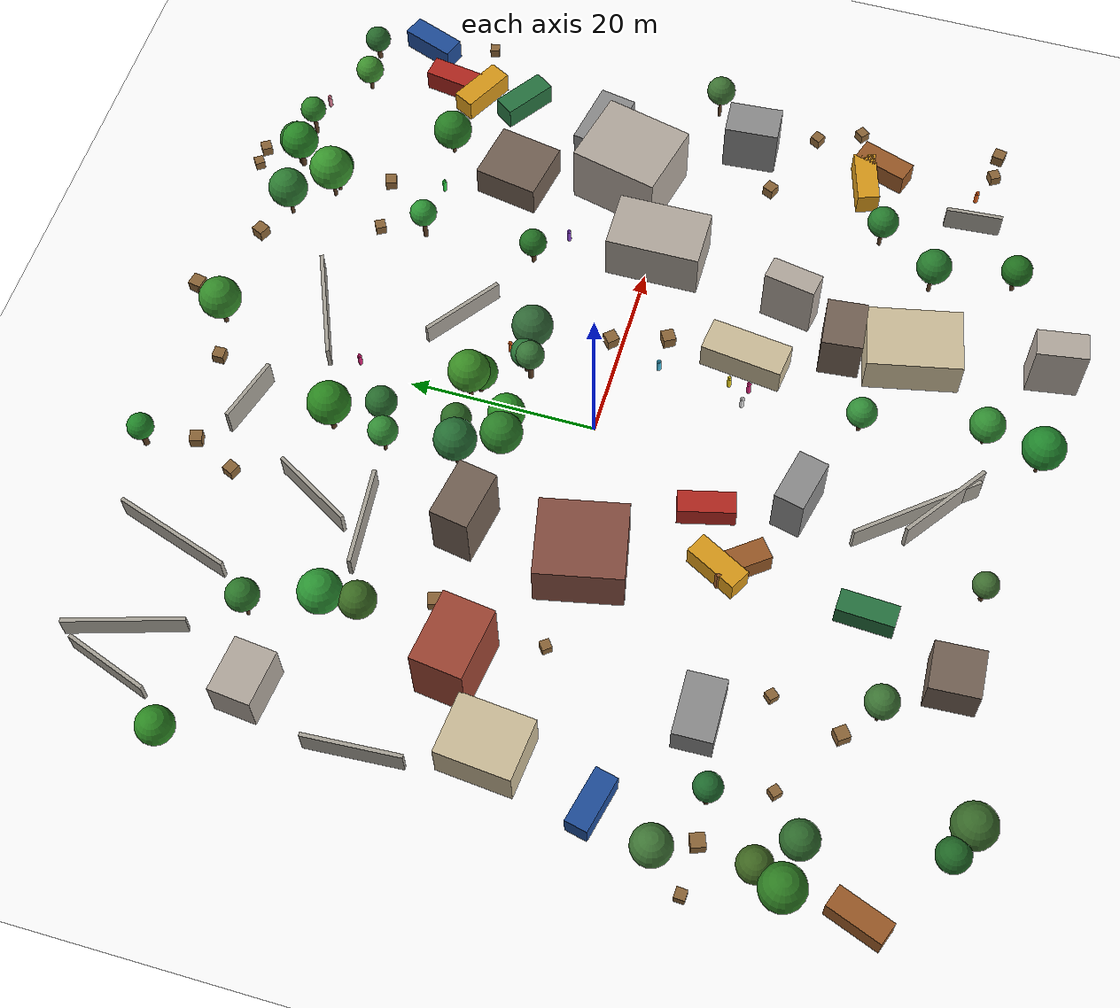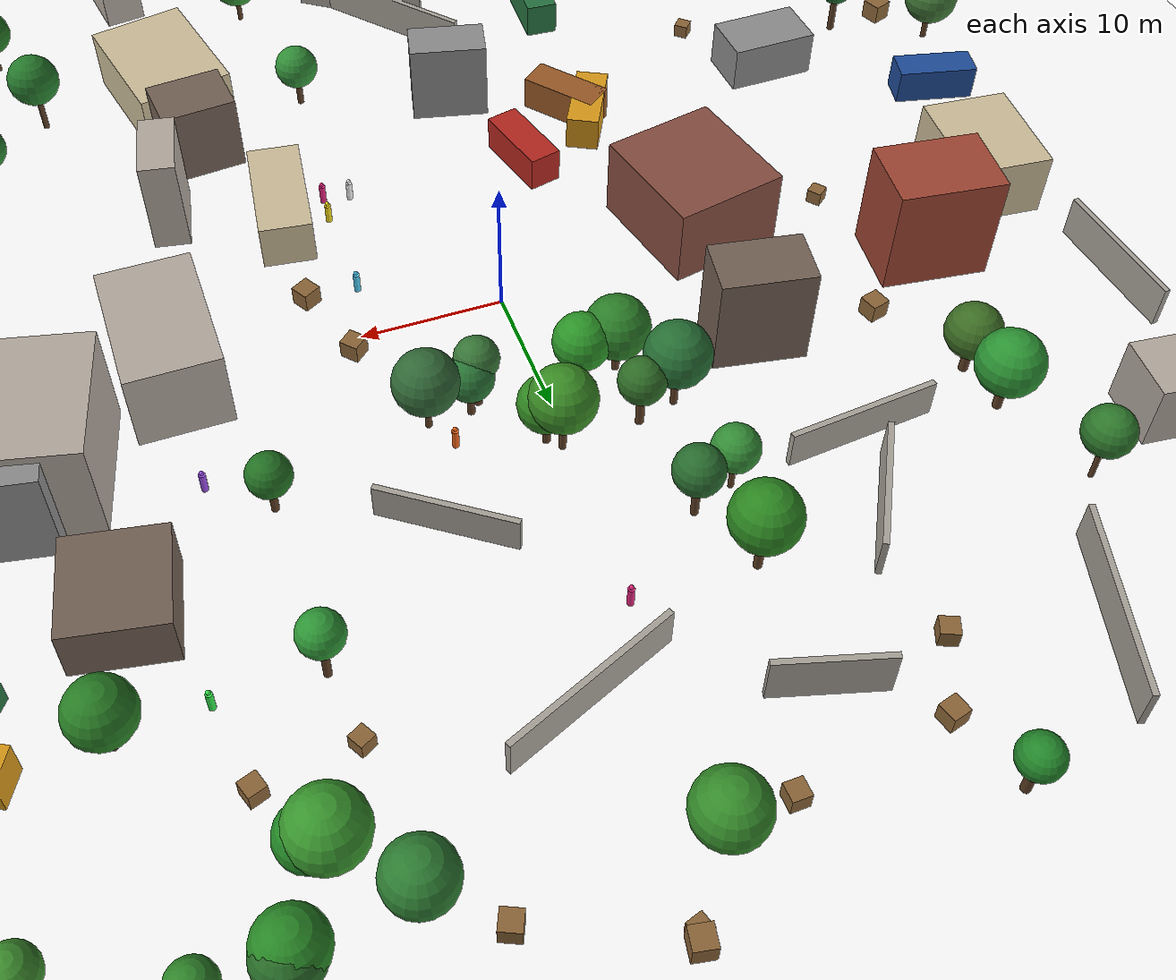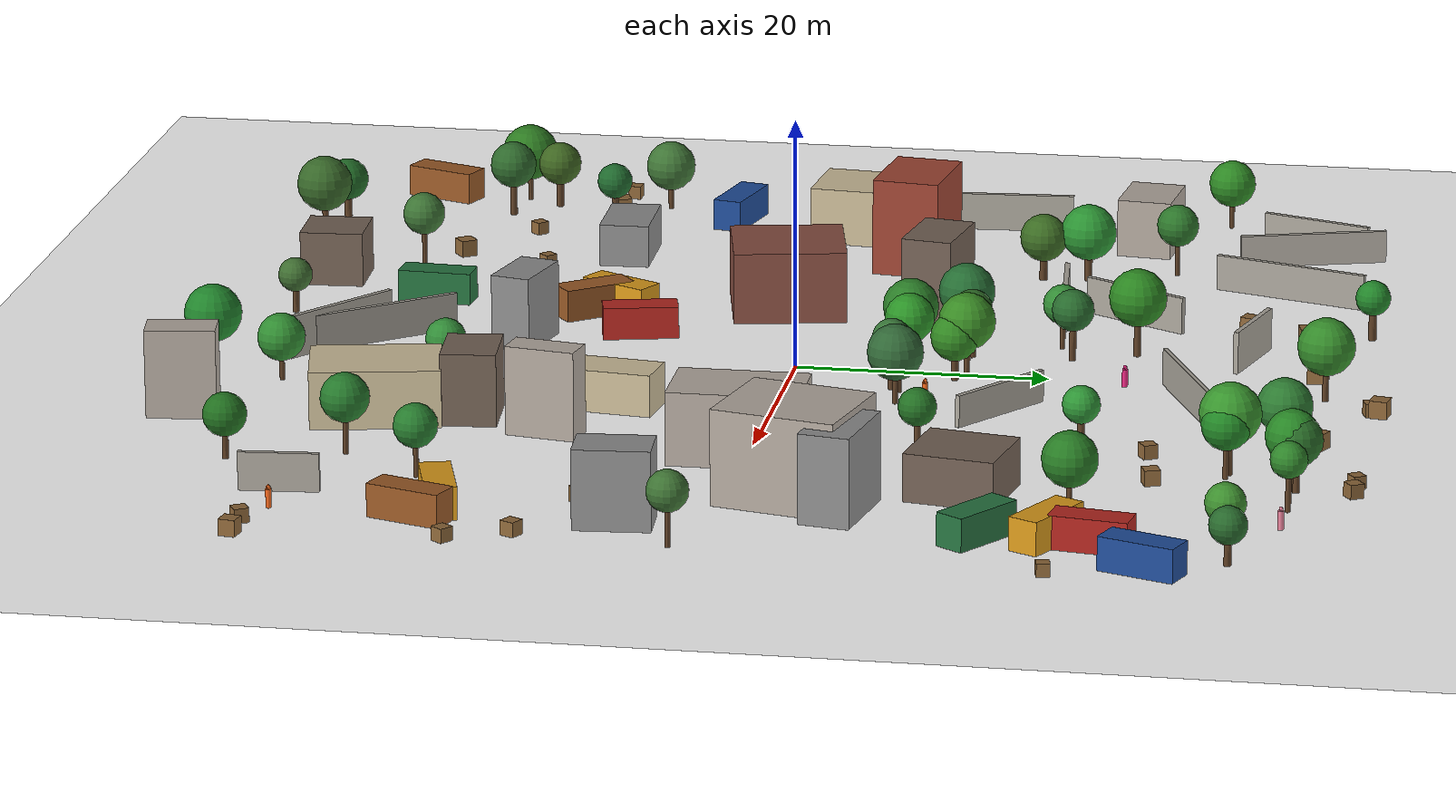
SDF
<?xml version="1.0" encoding="UTF-8"?>
<!-- Generated by sim/tools/generate_map.py; do not edit (regenerate instead).
     Physics, magnetic field and geodetic origin as PX4's default world. -->
<sdf version="1.9">
  <world name="map_11_high">
    <physics type="ode">
      <max_step_size>0.004</max_step_size>
      <real_time_factor>1.0</real_time_factor>
      <real_time_update_rate>250</real_time_update_rate>
    </physics>
    <gravity>0 0 -9.8</gravity>
    <magnetic_field>6e-06 2.3e-05 -4.2e-05</magnetic_field>
    <atmosphere type="adiabatic"/>
    <scene>
      <grid>false</grid>
      <ambient>0.55 0.55 0.58 1</ambient>
      <background>0.62 0.76 0.92 1</background>
      <shadows>false</shadows>
    </scene>
    <model name="ground_plane"><static>true</static><link name="link">
      <collision name="collision"><geometry><plane><normal>0 0 1</normal><size>1 1</size></plane></geometry></collision>
    </link></model>
    <include><uri>model://grass_ground</uri></include>
    <light name="sun" type="directional">
      <pose>0 0 500 0 0 0</pose>
      <cast_shadows>false</cast_shadows>
      <intensity>1.1</intensity>
      <direction>0.35 0.45 -0.82</direction>
      <diffuse>1.0 0.97 0.9 1</diffuse>
      <specular>0.25 0.25 0.25 1</specular>
    </light>
    <model name="building_0"><static>true</static><pose>-37.14 -0.07 2.35 0 0 1.478</pose><link name="link"><collision name="collision"><geometry><box><size>7.91 6.45 4.70</size></box></geometry></collision><visual name="visual"><geometry><box><size>7.91 6.45 4.70</size></box></geometry><material><diffuse>0.800 0.740 0.600 1</diffuse><ambient>0.640 0.592 0.480 1</ambient><specular>0.05 0.05 0.05 1</specular></material></visual></link></model>
    <model name="building_1"><static>true</static><pose>12.19 -13.10 1.67 0 0 1.443</pose><link name="link"><collision name="collision"><geometry><box><size>8.82 3.75 3.34</size></box></geometry></collision><visual name="visual"><geometry><box><size>8.82 3.75 3.34</size></box></geometry><material><diffuse>0.800 0.740 0.600 1</diffuse><ambient>0.640 0.592 0.480 1</ambient><specular>0.05 0.05 0.05 1</specular></material></visual></link></model>
    <model name="building_2"><static>true</static><pose>16.28 -22.47 2.86 0 0 0.096</pose><link name="link"><collision name="collision"><geometry><box><size>5.48 4.30 5.73</size></box></geometry></collision><visual name="visual"><geometry><box><size>5.48 4.30 5.73</size></box></geometry><material><diffuse>0.450 0.380 0.330 1</diffuse><ambient>0.360 0.304 0.264 1</ambient><specular>0.05 0.05 0.05 1</specular></material></visual></link></model>
    <model name="building_3"><static>true</static><pose>28.80 17.04 1.87 0 0 1.393</pose><link name="link"><collision name="collision"><geometry><box><size>7.01 6.54 3.75</size></box></geometry></collision><visual name="visual"><geometry><box><size>7.01 6.54 3.75</size></box></geometry><material><diffuse>0.450 0.380 0.330 1</diffuse><ambient>0.360 0.304 0.264 1</ambient><specular>0.05 0.05 0.05 1</specular></material></visual></link></model>
    <model name="building_4"><static>true</static><pose>31.67 4.91 3.74 0 0 -0.232</pose><link name="link"><collision name="collision"><geometry><box><size>8.42 9.73 7.47</size></box></geometry></collision><visual name="visual"><geometry><box><size>8.42 9.73 7.47</size></box></geometry><material><diffuse>0.700 0.660 0.620 1</diffuse><ambient>0.560 0.528 0.496 1</ambient><specular>0.05 0.05 0.05 1</specular></material></visual></link></model>
    <model name="building_5"><static>true</static><pose>-29.55 5.37 4.00 0 0 -0.128</pose><link name="link"><collision name="collision"><geometry><box><size>7.60 5.50 7.99</size></box></geometry></collision><visual name="visual"><geometry><box><size>7.60 5.50 7.99</size></box></geometry><material><diffuse>0.620 0.270 0.200 1</diffuse><ambient>0.496 0.216 0.160 1</ambient><specular>0.05 0.05 0.05 1</specular></material></visual></link></model>
    <model name="building_6"><static>true</static><pose>-14.67 9.16 3.68 0 0 -0.170</pose><link name="link"><collision name="collision"><geometry><box><size>6.45 4.11 7.35</size></box></geometry></collision><visual name="visual"><geometry><box><size>6.45 4.11 7.35</size></box></geometry><material><diffuse>0.450 0.380 0.330 1</diffuse><ambient>0.360 0.304 0.264 1</ambient><specular>0.05 0.05 0.05 1</specular></material></visual></link></model>
    <model name="building_7"><static>true</static><pose>-3.29 -22.29 3.03 0 0 -0.231</pose><link name="link"><collision name="collision"><geometry><box><size>5.74 3.22 6.05</size></box></geometry></collision><visual name="visual"><geometry><box><size>5.74 3.22 6.05</size></box></geometry><material><diffuse>0.550 0.550 0.550 1</diffuse><ambient>0.440 0.440 0.440 1</ambient><specular>0.05 0.05 0.05 1</specular></material></visual></link></model>
    <model name="building_8"><static>true</static><pose>39.59 -7.01 3.09 0 0 0.072</pose><link name="link"><collision name="collision"><geometry><box><size>3.92 5.84 6.18</size></box></geometry></collision><visual name="visual"><geometry><box><size>3.92 5.84 6.18</size></box></geometry><material><diffuse>0.550 0.550 0.550 1</diffuse><ambient>0.440 0.440 0.440 1</ambient><specular>0.05 0.05 0.05 1</specular></material></visual></link></model>
    <model name="building_9"><static>true</static><pose>17.34 -29.78 2.29 0 0 1.777</pose><link name="link"><collision name="collision"><geometry><box><size>10.08 7.07 4.58</size></box></geometry></collision><visual name="visual"><geometry><box><size>10.08 7.07 4.58</size></box></geometry><material><diffuse>0.800 0.740 0.600 1</diffuse><ambient>0.640 0.592 0.480 1</ambient><specular>0.05 0.05 0.05 1</specular></material></visual></link></model>
    <model name="building_10"><static>true</static><pose>-15.43 -3.11 2.90 0 0 1.774</pose><link name="link"><collision name="collision"><geometry><box><size>9.10 8.34 5.81</size></box></geometry></collision><visual name="visual"><geometry><box><size>9.10 8.34 5.81</size></box></geometry><material><diffuse>0.520 0.300 0.250 1</diffuse><ambient>0.416 0.240 0.200 1</ambient><specular>0.05 0.05 0.05 1</specular></material></visual></link></model>
    <model name="building_11"><static>true</static><pose>19.74 -16.07 3.52 0 0 1.393</pose><link name="link"><collision name="collision"><geometry><box><size>5.56 2.55 7.03</size></box></geometry></collision><visual name="visual"><geometry><box><size>5.56 2.55 7.03</size></box></geometry><material><diffuse>0.700 0.660 0.620 1</diffuse><ambient>0.560 0.528 0.496 1</ambient><specular>0.05 0.05 0.05 1</specular></material></visual></link></model>
    <model name="building_12"><static>true</static><pose>19.10 -44.53 3.50 0 0 1.723</pose><link name="link"><collision name="collision"><geometry><box><size>5.45 3.03 7.01</size></box></geometry></collision><visual name="visual"><geometry><box><size>5.45 3.03 7.01</size></box></geometry><material><diffuse>0.700 0.660 0.620 1</diffuse><ambient>0.560 0.528 0.496 1</ambient><specular>0.05 0.05 0.05 1</specular></material></visual></link></model>
    <model name="building_13"><static>true</static><pose>34.59 8.79 3.47 0 0 -0.181</pose><link name="link"><collision name="collision"><geometry><box><size>7.13 3.96 6.95</size></box></geometry></collision><visual name="visual"><geometry><box><size>7.13 3.96 6.95</size></box></geometry><material><diffuse>0.550 0.550 0.550 1</diffuse><ambient>0.440 0.440 0.440 1</ambient><specular>0.05 0.05 0.05 1</specular></material></visual></link></model>
    <model name="building_14"><static>true</static><pose>-18.26 -41.08 2.21 0 0 1.622</pose><link name="link"><collision name="collision"><geometry><box><size>5.15 5.05 4.43</size></box></geometry></collision><visual name="visual"><geometry><box><size>5.15 5.05 4.43</size></box></geometry><material><diffuse>0.450 0.380 0.330 1</diffuse><ambient>0.360 0.304 0.264 1</ambient><specular>0.05 0.05 0.05 1</specular></material></visual></link></model>
    <model name="building_15"><static>true</static><pose>-37.28 23.92 2.39 0 0 1.466</pose><link name="link"><collision name="collision"><geometry><box><size>4.48 5.85 4.79</size></box></geometry></collision><visual name="visual"><geometry><box><size>4.48 5.85 4.79</size></box></geometry><material><diffuse>0.700 0.660 0.620 1</diffuse><ambient>0.560 0.528 0.496 1</ambient><specular>0.05 0.05 0.05 1</specular></material></visual></link></model>
    <model name="building_16"><static>true</static><pose>22.71 -0.68 2.88 0 0 1.580</pose><link name="link"><collision name="collision"><geometry><box><size>10.15 6.34 5.77</size></box></geometry></collision><visual name="visual"><geometry><box><size>10.15 6.34 5.77</size></box></geometry><material><diffuse>0.700 0.660 0.620 1</diffuse><ambient>0.560 0.528 0.496 1</ambient><specular>0.05 0.05 0.05 1</specular></material></visual></link></model>
    <model name="building_17"><static>true</static><pose>-28.28 -18.48 1.74 0 0 1.595</pose><link name="link"><collision name="collision"><geometry><box><size>4.08 6.65 3.48</size></box></geometry></collision><visual name="visual"><geometry><box><size>4.08 6.65 3.48</size></box></geometry><material><diffuse>0.550 0.550 0.550 1</diffuse><ambient>0.440 0.440 0.440 1</ambient><specular>0.05 0.05 0.05 1</specular></material></visual></link></model>
    <model name="wall_0"><static>true</static><pose>-15.99 24.98 1.49 0 0 1.043</pose><link name="link"><collision name="collision"><geometry><box><size>9.46 0.40 2.99</size></box></geometry></collision><visual name="visual"><geometry><box><size>9.46 0.40 2.99</size></box></geometry><material><diffuse>0.660 0.640 0.600 1</diffuse><ambient>0.528 0.512 0.480 1</ambient><specular>0.05 0.05 0.05 1</specular></material></visual></link></model>
    <model name="wall_1"><static>true</static><pose>-34.68 37.65 1.33 0 0 1.866</pose><link name="link"><collision name="collision"><geometry><box><size>12.21 0.40 2.67</size></box></geometry></collision><visual name="visual"><geometry><box><size>12.21 0.40 2.67</size></box></geometry><material><diffuse>0.660 0.640 0.600 1</diffuse><ambient>0.528 0.512 0.480 1</ambient><specular>0.05 0.05 0.05 1</specular></material></visual></link></model>
    <model name="wall_2"><static>true</static><pose>5.51 31.46 1.45 0 0 0.400</pose><link name="link"><collision name="collision"><geometry><box><size>12.35 0.40 2.90</size></box></geometry></collision><visual name="visual"><geometry><box><size>12.35 0.40 2.90</size></box></geometry><material><diffuse>0.660 0.640 0.600 1</diffuse><ambient>0.528 0.512 0.480 1</ambient><specular>0.05 0.05 0.05 1</specular></material></visual></link></model>
    <model name="wall_3"><static>true</static><pose>-39.17 37.57 1.27 0 0 1.229</pose><link name="link"><collision name="collision"><geometry><box><size>9.34 0.40 2.53</size></box></geometry></collision><visual name="visual"><geometry><box><size>9.34 0.40 2.53</size></box></geometry><material><diffuse>0.660 0.640 0.600 1</diffuse><ambient>0.528 0.512 0.480 1</ambient><specular>0.05 0.05 0.05 1</specular></material></visual></link></model>
    <model name="wall_4"><static>true</static><pose>-40.90 11.93 1.54 0 0 1.630</pose><link name="link"><collision name="collision"><geometry><box><size>10.09 0.40 3.08</size></box></geometry></collision><visual name="visual"><geometry><box><size>10.09 0.40 3.08</size></box></geometry><material><diffuse>0.660 0.640 0.600 1</diffuse><ambient>0.528 0.512 0.480 1</ambient><specular>0.05 0.05 0.05 1</specular></material></visual></link></model>
    <model name="wall_5"><static>true</static><pose>-7.16 35.20 1.70 0 0 2.864</pose><link name="link"><collision name="collision"><geometry><box><size>7.24 0.40 3.40</size></box></geometry></collision><visual name="visual"><geometry><box><size>7.24 0.40 3.40</size></box></geometry><material><diffuse>0.660 0.640 0.600 1</diffuse><ambient>0.528 0.512 0.480 1</ambient><specular>0.05 0.05 0.05 1</specular></material></visual></link></model>
    <model name="wall_6"><static>true</static><pose>-0.06 -36.59 1.72 0 0 2.512</pose><link name="link"><collision name="collision"><geometry><box><size>10.61 0.40 3.44</size></box></geometry></collision><visual name="visual"><geometry><box><size>10.61 0.40 3.44</size></box></geometry><material><diffuse>0.660 0.640 0.600 1</diffuse><ambient>0.528 0.512 0.480 1</ambient><specular>0.05 0.05 0.05 1</specular></material></visual></link></model>
    <model name="wall_7"><static>true</static><pose>36.21 -32.88 1.49 0 0 1.646</pose><link name="link"><collision name="collision"><geometry><box><size>6.10 0.40 2.98</size></box></geometry></collision><visual name="visual"><geometry><box><size>6.10 0.40 2.98</size></box></geometry><material><diffuse>0.660 0.640 0.600 1</diffuse><ambient>0.528 0.512 0.480 1</ambient><specular>0.05 0.05 0.05 1</specular></material></visual></link></model>
    <model name="wall_8"><static>true</static><pose>-24.46 36.70 1.45 0 0 1.255</pose><link name="link"><collision name="collision"><geometry><box><size>12.90 0.40 2.90</size></box></geometry></collision><visual name="visual"><geometry><box><size>12.90 0.40 2.90</size></box></geometry><material><diffuse>0.660 0.640 0.600 1</diffuse><ambient>0.528 0.512 0.480 1</ambient><specular>0.05 0.05 0.05 1</specular></material></visual></link></model>
    <model name="wall_9"><static>true</static><pose>9.40 17.34 1.27 0 0 2.510</pose><link name="link"><collision name="collision"><geometry><box><size>9.36 0.40 2.54</size></box></geometry></collision><visual name="visual"><geometry><box><size>9.36 0.40 2.54</size></box></geometry><material><diffuse>0.660 0.640 0.600 1</diffuse><ambient>0.528 0.512 0.480 1</ambient><specular>0.05 0.05 0.05 1</specular></material></visual></link></model>
    <model name="wall_10"><static>true</static><pose>-17.50 19.16 1.37 0 0 0.092</pose><link name="link"><collision name="collision"><geometry><box><size>10.52 0.40 2.75</size></box></geometry></collision><visual name="visual"><geometry><box><size>10.52 0.40 2.75</size></box></geometry><material><diffuse>0.660 0.640 0.600 1</diffuse><ambient>0.528 0.512 0.480 1</ambient><specular>0.05 0.05 0.05 1</specular></material></visual></link></model>
    <model name="wall_11"><static>true</static><pose>-1.28 -34.03 1.48 0 0 2.255</pose><link name="link"><collision name="collision"><geometry><box><size>14.44 0.40 2.97</size></box></geometry></collision><visual name="visual"><geometry><box><size>14.44 0.40 2.97</size></box></geometry><material><diffuse>0.660 0.640 0.600 1</diffuse><ambient>0.528 0.512 0.480 1</ambient><specular>0.05 0.05 0.05 1</specular></material></visual></link></model>
    <model name="container_0"><static>true</static><pose>-6.40 -13.59 1.30 0 0 1.811</pose><link name="link"><collision name="collision"><geometry><box><size>6.00 2.40 2.60</size></box></geometry></collision><visual name="visual"><geometry><box><size>6.00 2.40 2.60</size></box></geometry><material><diffuse>0.700 0.150 0.120 1</diffuse><ambient>0.560 0.120 0.096 1</ambient><specular>0.05 0.05 0.05 1</specular></material></visual></link></model>
    <model name="container_1"><static>true</static><pose>-43.27 -37.23 1.30 0 0 1.210</pose><link name="link"><collision name="collision"><geometry><box><size>6.00 2.40 2.60</size></box></geometry></collision><visual name="visual"><geometry><box><size>6.00 2.40 2.60</size></box></geometry><material><diffuse>0.600 0.350 0.150 1</diffuse><ambient>0.480 0.280 0.120 1</ambient><specular>0.05 0.05 0.05 1</specular></material></visual></link></model>
    <model name="container_2"><static>true</static><pose>-12.53 -16.29 1.30 0 0 1.078</pose><link name="link"><collision name="collision"><geometry><box><size>6.00 2.40 2.60</size></box></geometry></collision><visual name="visual"><geometry><box><size>6.00 2.40 2.60</size></box></geometry><material><diffuse>0.850 0.600 0.100 1</diffuse><ambient>0.680 0.480 0.080 1</ambient><specular>0.05 0.05 0.05 1</specular></material></visual></link></model>
    <model name="container_3"><static>true</static><pose>-13.43 -31.58 1.30 0 0 1.517</pose><link name="link"><collision name="collision"><geometry><box><size>6.00 2.40 2.60</size></box></geometry></collision><visual name="visual"><geometry><box><size>6.00 2.40 2.60</size></box></geometry><material><diffuse>0.150 0.450 0.250 1</diffuse><ambient>0.120 0.360 0.200 1</ambient><specular>0.05 0.05 0.05 1</specular></material></visual></link></model>
    <model name="container_4"><static>true</static><pose>-11.52 -18.28 1.30 0 0 2.227</pose><link name="link"><collision name="collision"><geometry><box><size>6.00 2.40 2.60</size></box></geometry></collision><visual name="visual"><geometry><box><size>6.00 2.40 2.60</size></box></geometry><material><diffuse>0.600 0.350 0.150 1</diffuse><ambient>0.480 0.280 0.120 1</ambient><specular>0.05 0.05 0.05 1</specular></material></visual></link></model>
    <model name="container_5"><static>true</static><pose>38.93 24.59 1.30 0 0 2.662</pose><link name="link"><collision name="collision"><geometry><box><size>6.00 2.40 2.60</size></box></geometry></collision><visual name="visual"><geometry><box><size>6.00 2.40 2.60</size></box></geometry><material><diffuse>0.850 0.600 0.100 1</diffuse><ambient>0.680 0.480 0.080 1</ambient><specular>0.05 0.05 0.05 1</specular></material></visual></link></model>
    <model name="container_6"><static>true</static><pose>44.28 32.15 1.30 0 0 1.217</pose><link name="link"><collision name="collision"><geometry><box><size>6.00 2.40 2.60</size></box></geometry></collision><visual name="visual"><geometry><box><size>6.00 2.40 2.60</size></box></geometry><material><diffuse>0.120 0.300 0.600 1</diffuse><ambient>0.096 0.240 0.480 1</ambient><specular>0.05 0.05 0.05 1</specular></material></visual></link></model>
    <model name="container_7"><static>true</static><pose>-39.58 -11.09 1.30 0 0 2.912</pose><link name="link"><collision name="collision"><geometry><box><size>6.00 2.40 2.60</size></box></geometry></collision><visual name="visual"><geometry><box><size>6.00 2.40 2.60</size></box></geometry><material><diffuse>0.120 0.300 0.600 1</diffuse><ambient>0.096 0.240 0.480 1</ambient><specular>0.05 0.05 0.05 1</specular></material></visual></link></model>
    <model name="container_8"><static>true</static><pose>40.95 -21.92 1.30 0 0 1.240</pose><link name="link"><collision name="collision"><geometry><box><size>6.00 2.40 2.60</size></box></geometry></collision><visual name="visual"><geometry><box><size>6.00 2.40 2.60</size></box></geometry><material><diffuse>0.600 0.350 0.150 1</diffuse><ambient>0.480 0.280 0.120 1</ambient><specular>0.05 0.05 0.05 1</specular></material></visual></link></model>
    <model name="container_9"><static>true</static><pose>38.29 -20.42 1.30 0 0 0.291</pose><link name="link"><collision name="collision"><geometry><box><size>6.00 2.40 2.60</size></box></geometry></collision><visual name="visual"><geometry><box><size>6.00 2.40 2.60</size></box></geometry><material><diffuse>0.850 0.600 0.100 1</diffuse><ambient>0.680 0.480 0.080 1</ambient><specular>0.05 0.05 0.05 1</specular></material></visual></link></model>
    <model name="container_10"><static>true</static><pose>39.63 27.98 1.30 0 0 1.417</pose><link name="link"><collision name="collision"><geometry><box><size>6.00 2.40 2.60</size></box></geometry></collision><visual name="visual"><geometry><box><size>6.00 2.40 2.60</size></box></geometry><material><diffuse>0.700 0.150 0.120 1</diffuse><ambient>0.560 0.120 0.096 1</ambient><specular>0.05 0.05 0.05 1</specular></material></visual></link></model>
    <model name="container_11"><static>true</static><pose>39.05 19.55 1.30 0 0 2.541</pose><link name="link"><collision name="collision"><geometry><box><size>6.00 2.40 2.60</size></box></geometry></collision><visual name="visual"><geometry><box><size>6.00 2.40 2.60</size></box></geometry><material><diffuse>0.150 0.450 0.250 1</diffuse><ambient>0.120 0.360 0.200 1</ambient><specular>0.05 0.05 0.05 1</specular></material></visual></link></model>
    <model name="crate_0"><static>true</static><pose>5.35 46.17 0.70 0 0 2.957</pose><link name="link"><collision name="collision"><geometry><box><size>1.41 1.41 1.41</size></box></geometry></collision><visual name="visual"><geometry><box><size>1.41 1.41 1.41</size></box></geometry><material><diffuse>0.550 0.400 0.220 1</diffuse><ambient>0.440 0.320 0.176 1</ambient><specular>0.05 0.05 0.05 1</specular></material></visual></link></model>
    <model name="crate_1"><static>true</static><pose>10.81 1.24 0.66 0 0 2.306</pose><link name="link"><collision name="collision"><geometry><box><size>1.32 1.32 1.32</size></box></geometry></collision><visual name="visual"><geometry><box><size>1.32 1.32 1.32</size></box></geometry><material><diffuse>0.550 0.400 0.220 1</diffuse><ambient>0.440 0.320 0.176 1</ambient><specular>0.05 0.05 0.05 1</specular></material></visual></link></model>
    <model name="crate_2"><static>true</static><pose>-12.77 39.08 0.65 0 0 0.256</pose><link name="link"><collision name="collision"><geometry><box><size>1.29 1.29 1.29</size></box></geometry></collision><visual name="visual"><geometry><box><size>1.29 1.29 1.29</size></box></geometry><material><diffuse>0.550 0.400 0.220 1</diffuse><ambient>0.440 0.320 0.176 1</ambient><specular>0.05 0.05 0.05 1</specular></material></visual></link></model>
    <model name="crate_3"><static>true</static><pose>-24.14 -24.62 0.52 0 0 2.388</pose><link name="link"><collision name="collision"><geometry><box><size>1.03 1.03 1.03</size></box></geometry></collision><visual name="visual"><geometry><box><size>1.03 1.03 1.03</size></box></geometry><material><diffuse>0.550 0.400 0.220 1</diffuse><ambient>0.440 0.320 0.176 1</ambient><specular>0.05 0.05 0.05 1</specular></material></visual></link></model>
    <model name="crate_4"><static>true</static><pose>45.39 -18.60 0.55 0 0 2.481</pose><link name="link"><collision name="collision"><geometry><box><size>1.10 1.10 1.10</size></box></geometry></collision><visual name="visual"><geometry><box><size>1.10 1.10 1.10</size></box></geometry><material><diffuse>0.550 0.400 0.220 1</diffuse><ambient>0.440 0.320 0.176 1</ambient><specular>0.05 0.05 0.05 1</specular></material></visual></link></model>
    <model name="crate_5"><static>true</static><pose>-2.55 40.56 0.62 0 0 0.022</pose><link name="link"><collision name="collision"><geometry><box><size>1.23 1.23 1.23</size></box></geometry></collision><visual name="visual"><geometry><box><size>1.23 1.23 1.23</size></box></geometry><material><diffuse>0.550 0.400 0.220 1</diffuse><ambient>0.440 0.320 0.176 1</ambient><specular>0.05 0.05 0.05 1</specular></material></visual></link></model>
    <model name="crate_6"><static>true</static><pose>46.44 -34.09 0.64 0 0 1.392</pose><link name="link"><collision name="collision"><geometry><box><size>1.28 1.28 1.28</size></box></geometry></collision><visual name="visual"><geometry><box><size>1.28 1.28 1.28</size></box></geometry><material><diffuse>0.550 0.400 0.220 1</diffuse><ambient>0.440 0.320 0.176 1</ambient><specular>0.05 0.05 0.05 1</specular></material></visual></link></model>
    <model name="crate_7"><static>true</static><pose>-33.49 -27.17 0.52 0 0 0.820</pose><link name="link"><collision name="collision"><geometry><box><size>1.04 1.04 1.04</size></box></geometry></collision><visual name="visual"><geometry><box><size>1.04 1.04 1.04</size></box></geometry><material><diffuse>0.550 0.400 0.220 1</diffuse><ambient>0.440 0.320 0.176 1</ambient><specular>0.05 0.05 0.05 1</specular></material></visual></link></model>
    <model name="crate_8"><static>true</static><pose>43.33 -13.89 0.58 0 0 1.086</pose><link name="link"><collision name="collision"><geometry><box><size>1.15 1.15 1.15</size></box></geometry></collision><visual name="visual"><geometry><box><size>1.15 1.15 1.15</size></box></geometry><material><diffuse>0.550 0.400 0.220 1</diffuse><ambient>0.440 0.320 0.176 1</ambient><specular>0.05 0.05 0.05 1</specular></material></visual></link></model>
    <model name="crate_9"><static>true</static><pose>12.60 -4.55 0.68 0 0 0.526</pose><link name="link"><collision name="collision"><geometry><box><size>1.35 1.35 1.35</size></box></geometry></collision><visual name="visual"><geometry><box><size>1.35 1.35 1.35</size></box></geometry><material><diffuse>0.550 0.400 0.220 1</diffuse><ambient>0.440 0.320 0.176 1</ambient><specular>0.05 0.05 0.05 1</specular></material></visual></link></model>
    <model name="crate_10"><static>true</static><pose>24.31 30.61 0.61 0 0 1.906</pose><link name="link"><collision name="collision"><geometry><box><size>1.22 1.22 1.22</size></box></geometry></collision><visual name="visual"><geometry><box><size>1.22 1.22 1.22</size></box></geometry><material><diffuse>0.550 0.400 0.220 1</diffuse><ambient>0.440 0.320 0.176 1</ambient><specular>0.05 0.05 0.05 1</specular></material></visual></link></model>
    <model name="crate_11"><static>true</static><pose>-40.25 -21.45 0.74 0 0 0.361</pose><link name="link"><collision name="collision"><geometry><box><size>1.47 1.47 1.47</size></box></geometry></collision><visual name="visual"><geometry><box><size>1.47 1.47 1.47</size></box></geometry><material><diffuse>0.550 0.400 0.220 1</diffuse><ambient>0.440 0.320 0.176 1</ambient><specular>0.05 0.05 0.05 1</specular></material></visual></link></model>
    <model name="crate_12"><static>true</static><pose>22.80 45.77 0.52 0 0 0.602</pose><link name="link"><collision name="collision"><geometry><box><size>1.04 1.04 1.04</size></box></geometry></collision><visual name="visual"><geometry><box><size>1.04 1.04 1.04</size></box></geometry><material><diffuse>0.550 0.400 0.220 1</diffuse><ambient>0.440 0.320 0.176 1</ambient><specular>0.05 0.05 0.05 1</specular></material></visual></link></model>
    <model name="crate_13"><static>true</static><pose>18.11 29.73 0.56 0 0 0.511</pose><link name="link"><collision name="collision"><geometry><box><size>1.11 1.11 1.11</size></box></geometry></collision><visual name="visual"><geometry><box><size>1.11 1.11 1.11</size></box></geometry><material><diffuse>0.550 0.400 0.220 1</diffuse><ambient>0.440 0.320 0.176 1</ambient><specular>0.05 0.05 0.05 1</specular></material></visual></link></model>
    <model name="crate_14"><static>true</static><pose>-25.19 -2.30 0.52 0 0 0.658</pose><link name="link"><collision name="collision"><geometry><box><size>1.04 1.04 1.04</size></box></geometry></collision><visual name="visual"><geometry><box><size>1.04 1.04 1.04</size></box></geometry><material><diffuse>0.550 0.400 0.220 1</diffuse><ambient>0.440 0.320 0.176 1</ambient><specular>0.05 0.05 0.05 1</specular></material></visual></link></model>
    <model name="crate_15"><static>true</static><pose>-45.44 -21.21 0.56 0 0 1.507</pose><link name="link"><collision name="collision"><geometry><box><size>1.11 1.11 1.11</size></box></geometry></collision><visual name="visual"><geometry><box><size>1.11 1.11 1.11</size></box></geometry><material><diffuse>0.550 0.400 0.220 1</diffuse><ambient>0.440 0.320 0.176 1</ambient><specular>0.05 0.05 0.05 1</specular></material></visual></link></model>
    <model name="crate_16"><static>true</static><pose>13.90 42.16 0.66 0 0 1.143</pose><link name="link"><collision name="collision"><geometry><box><size>1.32 1.32 1.32</size></box></geometry></collision><visual name="visual"><geometry><box><size>1.32 1.32 1.32</size></box></geometry><material><diffuse>0.550 0.400 0.220 1</diffuse><ambient>0.440 0.320 0.176 1</ambient><specular>0.05 0.05 0.05 1</specular></material></visual></link></model>
    <model name="crate_17"><static>true</static><pose>5.16 45.47 0.54 0 0 0.297</pose><link name="link"><collision name="collision"><geometry><box><size>1.08 1.08 1.08</size></box></geometry></collision><visual name="visual"><geometry><box><size>1.08 1.08 1.08</size></box></geometry><material><diffuse>0.550 0.400 0.220 1</diffuse><ambient>0.440 0.320 0.176 1</ambient><specular>0.05 0.05 0.05 1</specular></material></visual></link></model>
    <model name="crate_18"><static>true</static><pose>43.57 -34.06 0.57 0 0 0.537</pose><link name="link"><collision name="collision"><geometry><box><size>1.13 1.13 1.13</size></box></geometry></collision><visual name="visual"><geometry><box><size>1.13 1.13 1.13</size></box></geometry><material><diffuse>0.550 0.400 0.220 1</diffuse><ambient>0.440 0.320 0.176 1</ambient><specular>0.05 0.05 0.05 1</specular></material></visual></link></model>
    <model name="crate_19"><static>true</static><pose>-15.19 34.31 0.62 0 0 2.737</pose><link name="link"><collision name="collision"><geometry><box><size>1.24 1.24 1.24</size></box></geometry></collision><visual name="visual"><geometry><box><size>1.24 1.24 1.24</size></box></geometry><material><diffuse>0.550 0.400 0.220 1</diffuse><ambient>0.440 0.320 0.176 1</ambient><specular>0.05 0.05 0.05 1</specular></material></visual></link></model>
    <model name="crate_20"><static>true</static><pose>-26.27 -31.94 0.68 0 0 0.638</pose><link name="link"><collision name="collision"><geometry><box><size>1.36 1.36 1.36</size></box></geometry></collision><visual name="visual"><geometry><box><size>1.36 1.36 1.36</size></box></geometry><material><diffuse>0.550 0.400 0.220 1</diffuse><ambient>0.440 0.320 0.176 1</ambient><specular>0.05 0.05 0.05 1</specular></material></visual></link></model>
    <model name="crate_21"><static>true</static><pose>45.93 25.23 0.51 0 0 0.212</pose><link name="link"><collision name="collision"><geometry><box><size>1.02 1.02 1.02</size></box></geometry></collision><visual name="visual"><geometry><box><size>1.02 1.02 1.02</size></box></geometry><material><diffuse>0.550 0.400 0.220 1</diffuse><ambient>0.440 0.320 0.176 1</ambient><specular>0.05 0.05 0.05 1</specular></material></visual></link></model>
    <model name="crate_22"><static>true</static><pose>34.94 -10.41 0.61 0 0 1.142</pose><link name="link"><collision name="collision"><geometry><box><size>1.22 1.22 1.22</size></box></geometry></collision><visual name="visual"><geometry><box><size>1.22 1.22 1.22</size></box></geometry><material><diffuse>0.550 0.400 0.220 1</diffuse><ambient>0.440 0.320 0.176 1</ambient><specular>0.05 0.05 0.05 1</specular></material></visual></link></model>
    <model name="crate_23"><static>true</static><pose>-23.57 9.59 0.67 0 0 0.264</pose><link name="link"><collision name="collision"><geometry><box><size>1.34 1.34 1.34</size></box></geometry></collision><visual name="visual"><geometry><box><size>1.34 1.34 1.34</size></box></geometry><material><diffuse>0.550 0.400 0.220 1</diffuse><ambient>0.440 0.320 0.176 1</ambient><specular>0.05 0.05 0.05 1</specular></material></visual></link></model>
    <model name="crate_24"><static>true</static><pose>24.94 45.72 0.56 0 0 2.154</pose><link name="link"><collision name="collision"><geometry><box><size>1.13 1.13 1.13</size></box></geometry></collision><visual name="visual"><geometry><box><size>1.13 1.13 1.13</size></box></geometry><material><diffuse>0.550 0.400 0.220 1</diffuse><ambient>0.440 0.320 0.176 1</ambient><specular>0.05 0.05 0.05 1</specular></material></visual></link></model>
    <model name="tree_0"><static>true</static><pose>-38.67 -30.45 0 0 0 0</pose><link name="link"><collision name="trunk"><pose>0 0 1.52 0 0 0</pose><geometry><cylinder><radius>0.28</radius><length>3.04</length></cylinder></geometry></collision><visual name="trunk"><pose>0 0 1.52 0 0 0</pose><geometry><cylinder><radius>0.28</radius><length>3.04</length></cylinder></geometry><material><diffuse>0.360 0.240 0.140 1</diffuse><ambient>0.288 0.192 0.112 1</ambient><specular>0.05 0.05 0.05 1</specular></material></visual><collision name="canopy"><pose>0 0 4.39 0 0 0</pose><geometry><sphere><radius>1.92</radius></sphere></geometry></collision><visual name="canopy"><pose>0 0 4.39 0 0 0</pose><geometry><sphere><radius>1.92</radius></sphere></geometry><material><diffuse>0.182 0.416 0.174 1</diffuse><ambient>0.146 0.333 0.139 1</ambient><specular>0.05 0.05 0.05 1</specular></material></visual></link></model>
    <model name="tree_1"><static>true</static><pose>37.08 37.37 0 0 0 0</pose><link name="link"><collision name="trunk"><pose>0 0 1.02 0 0 0</pose><geometry><cylinder><radius>0.21</radius><length>2.04</length></cylinder></geometry></collision><visual name="trunk"><pose>0 0 1.02 0 0 0</pose><geometry><cylinder><radius>0.21</radius><length>2.04</length></cylinder></geometry><material><diffuse>0.360 0.240 0.140 1</diffuse><ambient>0.288 0.192 0.112 1</ambient><specular>0.05 0.05 0.05 1</specular></material></visual><collision name="canopy"><pose>0 0 3.12 0 0 0</pose><geometry><sphere><radius>1.54</radius></sphere></geometry></collision><visual name="canopy"><pose>0 0 3.12 0 0 0</pose><geometry><sphere><radius>1.54</radius></sphere></geometry><material><diffuse>0.242 0.566 0.183 1</diffuse><ambient>0.193 0.453 0.147 1</ambient><specular>0.05 0.05 0.05 1</specular></material></visual></link></model>
    <model name="tree_2"><static>true</static><pose>-4.82 13.30 0 0 0 0</pose><link name="link"><collision name="trunk"><pose>0 0 1.40 0 0 0</pose><geometry><cylinder><radius>0.28</radius><length>2.81</length></cylinder></geometry></collision><visual name="trunk"><pose>0 0 1.40 0 0 0</pose><geometry><cylinder><radius>0.28</radius><length>2.81</length></cylinder></geometry><material><diffuse>0.360 0.240 0.140 1</diffuse><ambient>0.288 0.192 0.112 1</ambient><specular>0.05 0.05 0.05 1</specular></material></visual><collision name="canopy"><pose>0 0 3.92 0 0 0</pose><geometry><sphere><radius>1.60</radius></sphere></geometry></collision><visual name="canopy"><pose>0 0 3.92 0 0 0</pose><geometry><sphere><radius>1.60</radius></sphere></geometry><material><diffuse>0.180 0.424 0.149 1</diffuse><ambient>0.144 0.339 0.119 1</ambient><specular>0.05 0.05 0.05 1</specular></material></visual></link></model>
    <model name="tree_3"><static>true</static><pose>24.60 41.42 0 0 0 0</pose><link name="link"><collision name="trunk"><pose>0 0 1.35 0 0 0</pose><geometry><cylinder><radius>0.25</radius><length>2.70</length></cylinder></geometry></collision><visual name="trunk"><pose>0 0 1.35 0 0 0</pose><geometry><cylinder><radius>0.25</radius><length>2.70</length></cylinder></geometry><material><diffuse>0.360 0.240 0.140 1</diffuse><ambient>0.288 0.192 0.112 1</ambient><specular>0.05 0.05 0.05 1</specular></material></visual><collision name="canopy"><pose>0 0 4.08 0 0 0</pose><geometry><sphere><radius>1.97</radius></sphere></geometry></collision><visual name="canopy"><pose>0 0 4.08 0 0 0</pose><geometry><sphere><radius>1.97</radius></sphere></geometry><material><diffuse>0.159 0.425 0.154 1</diffuse><ambient>0.127 0.340 0.123 1</ambient><specular>0.05 0.05 0.05 1</specular></material></visual></link></model>
    <model name="tree_4"><static>true</static><pose>26.88 -29.96 0 0 0 0</pose><link name="link"><collision name="trunk"><pose>0 0 1.56 0 0 0</pose><geometry><cylinder><radius>0.21</radius><length>3.12</length></cylinder></geometry></collision><visual name="trunk"><pose>0 0 1.56 0 0 0</pose><geometry><cylinder><radius>0.21</radius><length>3.12</length></cylinder></geometry><material><diffuse>0.360 0.240 0.140 1</diffuse><ambient>0.288 0.192 0.112 1</ambient><specular>0.05 0.05 0.05 1</specular></material></visual><collision name="canopy"><pose>0 0 4.44 0 0 0</pose><geometry><sphere><radius>1.89</radius></sphere></geometry></collision><visual name="canopy"><pose>0 0 4.44 0 0 0</pose><geometry><sphere><radius>1.89</radius></sphere></geometry><material><diffuse>0.149 0.479 0.174 1</diffuse><ambient>0.119 0.383 0.139 1</ambient><specular>0.05 0.05 0.05 1</specular></material></visual></link></model>
    <model name="tree_5"><static>true</static><pose>8.02 9.05 0 0 0 0</pose><link name="link"><collision name="trunk"><pose>0 0 1.30 0 0 0</pose><geometry><cylinder><radius>0.22</radius><length>2.59</length></cylinder></geometry></collision><visual name="trunk"><pose>0 0 1.30 0 0 0</pose><geometry><cylinder><radius>0.22</radius><length>2.59</length></cylinder></geometry><material><diffuse>0.360 0.240 0.140 1</diffuse><ambient>0.288 0.192 0.112 1</ambient><specular>0.05 0.05 0.05 1</specular></material></visual><collision name="canopy"><pose>0 0 4.14 0 0 0</pose><geometry><sphere><radius>2.20</radius></sphere></geometry></collision><visual name="canopy"><pose>0 0 4.14 0 0 0</pose><geometry><sphere><radius>2.20</radius></sphere></geometry><material><diffuse>0.192 0.410 0.215 1</diffuse><ambient>0.153 0.328 0.172 1</ambient><specular>0.05 0.05 0.05 1</specular></material></visual></link></model>
    <model name="tree_6"><static>true</static><pose>-8.12 -42.12 0 0 0 0</pose><link name="link"><collision name="trunk"><pose>0 0 1.09 0 0 0</pose><geometry><cylinder><radius>0.26</radius><length>2.18</length></cylinder></geometry></collision><visual name="trunk"><pose>0 0 1.09 0 0 0</pose><geometry><cylinder><radius>0.26</radius><length>2.18</length></cylinder></geometry><material><diffuse>0.360 0.240 0.140 1</diffuse><ambient>0.288 0.192 0.112 1</ambient><specular>0.05 0.05 0.05 1</specular></material></visual><collision name="canopy"><pose>0 0 3.14 0 0 0</pose><geometry><sphere><radius>1.37</radius></sphere></geometry></collision><visual name="canopy"><pose>0 0 3.14 0 0 0</pose><geometry><sphere><radius>1.37</radius></sphere></geometry><material><diffuse>0.248 0.434 0.193 1</diffuse><ambient>0.198 0.347 0.154 1</ambient><specular>0.05 0.05 0.05 1</specular></material></visual></link></model>
    <model name="tree_7"><static>true</static><pose>-5.11 8.36 0 0 0 0</pose><link name="link"><collision name="trunk"><pose>0 0 1.15 0 0 0</pose><geometry><cylinder><radius>0.25</radius><length>2.31</length></cylinder></geometry></collision><visual name="trunk"><pose>0 0 1.15 0 0 0</pose><geometry><cylinder><radius>0.25</radius><length>2.31</length></cylinder></geometry><material><diffuse>0.360 0.240 0.140 1</diffuse><ambient>0.288 0.192 0.112 1</ambient><specular>0.05 0.05 0.05 1</specular></material></visual><collision name="canopy"><pose>0 0 3.85 0 0 0</pose><geometry><sphere><radius>2.21</radius></sphere></geometry></collision><visual name="canopy"><pose>0 0 3.85 0 0 0</pose><geometry><sphere><radius>2.21</radius></sphere></geometry><material><diffuse>0.169 0.496 0.157 1</diffuse><ambient>0.135 0.397 0.126 1</ambient><specular>0.05 0.05 0.05 1</specular></material></visual></link></model>
    <model name="tree_8"><static>true</static><pose>-44.38 29.99 0 0 0 0</pose><link name="link"><collision name="trunk"><pose>0 0 1.25 0 0 0</pose><geometry><cylinder><radius>0.21</radius><length>2.50</length></cylinder></geometry></collision><visual name="trunk"><pose>0 0 1.25 0 0 0</pose><geometry><cylinder><radius>0.21</radius><length>2.50</length></cylinder></geometry><material><diffuse>0.360 0.240 0.140 1</diffuse><ambient>0.288 0.192 0.112 1</ambient><specular>0.05 0.05 0.05 1</specular></material></visual><collision name="canopy"><pose>0 0 3.85 0 0 0</pose><geometry><sphere><radius>1.93</radius></sphere></geometry></collision><visual name="canopy"><pose>0 0 3.85 0 0 0</pose><geometry><sphere><radius>1.93</radius></sphere></geometry><material><diffuse>0.177 0.538 0.140 1</diffuse><ambient>0.141 0.430 0.112 1</ambient><specular>0.05 0.05 0.05 1</specular></material></visual></link></model>
    <model name="tree_9"><static>true</static><pose>7.83 -44.89 0 0 0 0</pose><link name="link"><collision name="trunk"><pose>0 0 1.50 0 0 0</pose><geometry><cylinder><radius>0.19</radius><length>3.00</length></cylinder></geometry></collision><visual name="trunk"><pose>0 0 1.50 0 0 0</pose><geometry><cylinder><radius>0.19</radius><length>3.00</length></cylinder></geometry><material><diffuse>0.360 0.240 0.140 1</diffuse><ambient>0.288 0.192 0.112 1</ambient><specular>0.05 0.05 0.05 1</specular></material></visual><collision name="canopy"><pose>0 0 4.59 0 0 0</pose><geometry><sphere><radius>2.27</radius></sphere></geometry></collision><visual name="canopy"><pose>0 0 4.59 0 0 0</pose><geometry><sphere><radius>2.27</radius></sphere></geometry><material><diffuse>0.129 0.526 0.175 1</diffuse><ambient>0.103 0.421 0.140 1</ambient><specular>0.05 0.05 0.05 1</specular></material></visual></link></model>
    <model name="tree_10"><static>true</static><pose>-26.79 16.22 0 0 0 0</pose><link name="link"><collision name="trunk"><pose>0 0 1.11 0 0 0</pose><geometry><cylinder><radius>0.32</radius><length>2.23</length></cylinder></geometry></collision><visual name="trunk"><pose>0 0 1.11 0 0 0</pose><geometry><cylinder><radius>0.32</radius><length>2.23</length></cylinder></geometry><material><diffuse>0.360 0.240 0.140 1</diffuse><ambient>0.288 0.192 0.112 1</ambient><specular>0.05 0.05 0.05 1</specular></material></visual><collision name="canopy"><pose>0 0 3.58 0 0 0</pose><geometry><sphere><radius>1.93</radius></sphere></geometry></collision><visual name="canopy"><pose>0 0 3.58 0 0 0</pose><geometry><sphere><radius>1.93</radius></sphere></geometry><material><diffuse>0.235 0.426 0.137 1</diffuse><ambient>0.188 0.341 0.110 1</ambient><specular>0.05 0.05 0.05 1</specular></material></visual></link></model>
    <model name="tree_11"><static>true</static><pose>1.35 12.76 0 0 0 0</pose><link name="link"><collision name="trunk"><pose>0 0 1.10 0 0 0</pose><geometry><cylinder><radius>0.27</radius><length>2.20</length></cylinder></geometry></collision><visual name="trunk"><pose>0 0 1.10 0 0 0</pose><geometry><cylinder><radius>0.27</radius><length>2.20</length></cylinder></geometry><material><diffuse>0.360 0.240 0.140 1</diffuse><ambient>0.288 0.192 0.112 1</ambient><specular>0.05 0.05 0.05 1</specular></material></visual><collision name="canopy"><pose>0 0 3.53 0 0 0</pose><geometry><sphere><radius>1.91</radius></sphere></geometry></collision><visual name="canopy"><pose>0 0 3.53 0 0 0</pose><geometry><sphere><radius>1.91</radius></sphere></geometry><material><diffuse>0.196 0.535 0.133 1</diffuse><ambient>0.157 0.428 0.106 1</ambient><specular>0.05 0.05 0.05 1</specular></material></visual></link></model>
    <model name="tree_12"><static>true</static><pose>-41.83 -27.06 0 0 0 0</pose><link name="link"><collision name="trunk"><pose>0 0 1.25 0 0 0</pose><geometry><cylinder><radius>0.29</radius><length>2.51</length></cylinder></geometry></collision><visual name="trunk"><pose>0 0 1.25 0 0 0</pose><geometry><cylinder><radius>0.29</radius><length>2.51</length></cylinder></geometry><material><diffuse>0.360 0.240 0.140 1</diffuse><ambient>0.288 0.192 0.112 1</ambient><specular>0.05 0.05 0.05 1</specular></material></visual><collision name="canopy"><pose>0 0 3.76 0 0 0</pose><geometry><sphere><radius>1.79</radius></sphere></geometry></collision><visual name="canopy"><pose>0 0 3.76 0 0 0</pose><geometry><sphere><radius>1.79</radius></sphere></geometry><material><diffuse>0.246 0.402 0.128 1</diffuse><ambient>0.197 0.322 0.102 1</ambient><specular>0.05 0.05 0.05 1</specular></material></visual></link></model>
    <model name="tree_13"><static>true</static><pose>-2.56 8.63 0 0 0 0</pose><link name="link"><collision name="trunk"><pose>0 0 1.15 0 0 0</pose><geometry><cylinder><radius>0.27</radius><length>2.31</length></cylinder></geometry></collision><visual name="trunk"><pose>0 0 1.15 0 0 0</pose><geometry><cylinder><radius>0.27</radius><length>2.31</length></cylinder></geometry><material><diffuse>0.360 0.240 0.140 1</diffuse><ambient>0.288 0.192 0.112 1</ambient><specular>0.05 0.05 0.05 1</specular></material></visual><collision name="canopy"><pose>0 0 3.68 0 0 0</pose><geometry><sphere><radius>1.96</radius></sphere></geometry></collision><visual name="canopy"><pose>0 0 3.68 0 0 0</pose><geometry><sphere><radius>1.96</radius></sphere></geometry><material><diffuse>0.172 0.582 0.154 1</diffuse><ambient>0.138 0.465 0.124 1</ambient><specular>0.05 0.05 0.05 1</specular></material></visual></link></model>
    <model name="tree_14"><static>true</static><pose>9.66 -39.00 0 0 0 0</pose><link name="link"><collision name="trunk"><pose>0 0 1.09 0 0 0</pose><geometry><cylinder><radius>0.19</radius><length>2.17</length></cylinder></geometry></collision><visual name="trunk"><pose>0 0 1.09 0 0 0</pose><geometry><cylinder><radius>0.19</radius><length>2.17</length></cylinder></geometry><material><diffuse>0.360 0.240 0.140 1</diffuse><ambient>0.288 0.192 0.112 1</ambient><specular>0.05 0.05 0.05 1</specular></material></visual><collision name="canopy"><pose>0 0 3.48 0 0 0</pose><geometry><sphere><radius>1.87</radius></sphere></geometry></collision><visual name="canopy"><pose>0 0 3.48 0 0 0</pose><geometry><sphere><radius>1.87</radius></sphere></geometry><material><diffuse>0.192 0.555 0.196 1</diffuse><ambient>0.154 0.444 0.157 1</ambient><specular>0.05 0.05 0.05 1</specular></material></visual></link></model>
    <model name="tree_15"><static>true</static><pose>18.84 12.31 0 0 0 0</pose><link name="link"><collision name="trunk"><pose>0 0 1.14 0 0 0</pose><geometry><cylinder><radius>0.25</radius><length>2.29</length></cylinder></geometry></collision><visual name="trunk"><pose>0 0 1.14 0 0 0</pose><geometry><cylinder><radius>0.25</radius><length>2.29</length></cylinder></geometry><material><diffuse>0.360 0.240 0.140 1</diffuse><ambient>0.288 0.192 0.112 1</ambient><specular>0.05 0.05 0.05 1</specular></material></visual><collision name="canopy"><pose>0 0 3.32 0 0 0</pose><geometry><sphere><radius>1.48</radius></sphere></geometry></collision><visual name="canopy"><pose>0 0 3.32 0 0 0</pose><geometry><sphere><radius>1.48</radius></sphere></geometry><material><diffuse>0.137 0.445 0.140 1</diffuse><ambient>0.109 0.356 0.112 1</ambient><specular>0.05 0.05 0.05 1</specular></material></visual></link></model>
    <model name="tree_16"><static>true</static><pose>-14.40 44.09 0 0 0 0</pose><link name="link"><collision name="trunk"><pose>0 0 1.24 0 0 0</pose><geometry><cylinder><radius>0.31</radius><length>2.49</length></cylinder></geometry></collision><visual name="trunk"><pose>0 0 1.24 0 0 0</pose><geometry><cylinder><radius>0.31</radius><length>2.49</length></cylinder></geometry><material><diffuse>0.360 0.240 0.140 1</diffuse><ambient>0.288 0.192 0.112 1</ambient><specular>0.05 0.05 0.05 1</specular></material></visual><collision name="canopy"><pose>0 0 3.47 0 0 0</pose><geometry><sphere><radius>1.40</radius></sphere></geometry></collision><visual name="canopy"><pose>0 0 3.47 0 0 0</pose><geometry><sphere><radius>1.40</radius></sphere></geometry><material><diffuse>0.135 0.528 0.166 1</diffuse><ambient>0.108 0.422 0.133 1</ambient><specular>0.05 0.05 0.05 1</specular></material></visual></link></model>
    <model name="tree_17"><static>true</static><pose>44.20 -2.22 0 0 0 0</pose><link name="link"><collision name="trunk"><pose>0 0 1.59 0 0 0</pose><geometry><cylinder><radius>0.18</radius><length>3.18</length></cylinder></geometry></collision><visual name="trunk"><pose>0 0 1.59 0 0 0</pose><geometry><cylinder><radius>0.18</radius><length>3.18</length></cylinder></geometry><material><diffuse>0.360 0.240 0.140 1</diffuse><ambient>0.288 0.192 0.112 1</ambient><specular>0.05 0.05 0.05 1</specular></material></visual><collision name="canopy"><pose>0 0 4.28 0 0 0</pose><geometry><sphere><radius>1.58</radius></sphere></geometry></collision><visual name="canopy"><pose>0 0 4.28 0 0 0</pose><geometry><sphere><radius>1.58</radius></sphere></geometry><material><diffuse>0.243 0.453 0.203 1</diffuse><ambient>0.194 0.362 0.163 1</ambient><specular>0.05 0.05 0.05 1</specular></material></visual></link></model>
    <model name="tree_18"><static>true</static><pose>2.13 41.73 0 0 0 0</pose><link name="link"><collision name="trunk"><pose>0 0 1.40 0 0 0</pose><geometry><cylinder><radius>0.24</radius><length>2.81</length></cylinder></geometry></collision><visual name="trunk"><pose>0 0 1.40 0 0 0</pose><geometry><cylinder><radius>0.24</radius><length>2.81</length></cylinder></geometry><material><diffuse>0.360 0.240 0.140 1</diffuse><ambient>0.288 0.192 0.112 1</ambient><specular>0.05 0.05 0.05 1</specular></material></visual><collision name="canopy"><pose>0 0 4.39 0 0 0</pose><geometry><sphere><radius>2.25</radius></sphere></geometry></collision><visual name="canopy"><pose>0 0 4.39 0 0 0</pose><geometry><sphere><radius>2.25</radius></sphere></geometry><material><diffuse>0.205 0.546 0.164 1</diffuse><ambient>0.164 0.437 0.131 1</ambient><specular>0.05 0.05 0.05 1</specular></material></visual></link></model>
    <model name="tree_19"><static>true</static><pose>17.72 39.91 0 0 0 0</pose><link name="link"><collision name="trunk"><pose>0 0 1.48 0 0 0</pose><geometry><cylinder><radius>0.20</radius><length>2.97</length></cylinder></geometry></collision><visual name="trunk"><pose>0 0 1.48 0 0 0</pose><geometry><cylinder><radius>0.20</radius><length>2.97</length></cylinder></geometry><material><diffuse>0.360 0.240 0.140 1</diffuse><ambient>0.288 0.192 0.112 1</ambient><specular>0.05 0.05 0.05 1</specular></material></visual><collision name="canopy"><pose>0 0 4.46 0 0 0</pose><geometry><sphere><radius>2.13</radius></sphere></geometry></collision><visual name="canopy"><pose>0 0 4.46 0 0 0</pose><geometry><sphere><radius>2.13</radius></sphere></geometry><material><diffuse>0.177 0.488 0.196 1</diffuse><ambient>0.142 0.391 0.157 1</ambient><specular>0.05 0.05 0.05 1</specular></material></visual></link></model>
    <model name="tree_20"><static>true</static><pose>-7.15 26.12 0 0 0 0</pose><link name="link"><collision name="trunk"><pose>0 0 1.59 0 0 0</pose><geometry><cylinder><radius>0.28</radius><length>3.19</length></cylinder></geometry></collision><visual name="trunk"><pose>0 0 1.59 0 0 0</pose><geometry><cylinder><radius>0.28</radius><length>3.19</length></cylinder></geometry><material><diffuse>0.360 0.240 0.140 1</diffuse><ambient>0.288 0.192 0.112 1</ambient><specular>0.05 0.05 0.05 1</specular></material></visual><collision name="canopy"><pose>0 0 4.79 0 0 0</pose><geometry><sphere><radius>2.29</radius></sphere></geometry></collision><visual name="canopy"><pose>0 0 4.79 0 0 0</pose><geometry><sphere><radius>2.29</radius></sphere></geometry><material><diffuse>0.170 0.527 0.128 1</diffuse><ambient>0.136 0.422 0.103 1</ambient><specular>0.05 0.05 0.05 1</specular></material></visual></link></model>
    <model name="tree_21"><static>true</static><pose>30.85 25.32 0 0 0 0</pose><link name="link"><collision name="trunk"><pose>0 0 1.15 0 0 0</pose><geometry><cylinder><radius>0.20</radius><length>2.31</length></cylinder></geometry></collision><visual name="trunk"><pose>0 0 1.15 0 0 0</pose><geometry><cylinder><radius>0.20</radius><length>2.31</length></cylinder></geometry><material><diffuse>0.360 0.240 0.140 1</diffuse><ambient>0.288 0.192 0.112 1</ambient><specular>0.05 0.05 0.05 1</specular></material></visual><collision name="canopy"><pose>0 0 3.79 0 0 0</pose><geometry><sphere><radius>2.12</radius></sphere></geometry></collision><visual name="canopy"><pose>0 0 3.79 0 0 0</pose><geometry><sphere><radius>2.12</radius></sphere></geometry><material><diffuse>0.156 0.489 0.143 1</diffuse><ambient>0.125 0.391 0.114 1</ambient><specular>0.05 0.05 0.05 1</specular></material></visual></link></model>
    <model name="tree_22"><static>true</static><pose>-27.16 19.87 0 0 0 0</pose><link name="link"><collision name="trunk"><pose>0 0 1.26 0 0 0</pose><geometry><cylinder><radius>0.31</radius><length>2.51</length></cylinder></geometry></collision><visual name="trunk"><pose>0 0 1.26 0 0 0</pose><geometry><cylinder><radius>0.31</radius><length>2.51</length></cylinder></geometry><material><diffuse>0.360 0.240 0.140 1</diffuse><ambient>0.288 0.192 0.112 1</ambient><specular>0.05 0.05 0.05 1</specular></material></visual><collision name="canopy"><pose>0 0 4.10 0 0 0</pose><geometry><sphere><radius>2.27</radius></sphere></geometry></collision><visual name="canopy"><pose>0 0 4.10 0 0 0</pose><geometry><sphere><radius>2.27</radius></sphere></geometry><material><diffuse>0.170 0.580 0.200 1</diffuse><ambient>0.136 0.464 0.160 1</ambient><specular>0.05 0.05 0.05 1</specular></material></visual></link></model>
    <model name="tree_23"><static>true</static><pose>4.42 8.23 0 0 0 0</pose><link name="link"><collision name="trunk"><pose>0 0 1.55 0 0 0</pose><geometry><cylinder><radius>0.29</radius><length>3.10</length></cylinder></geometry></collision><visual name="trunk"><pose>0 0 1.55 0 0 0</pose><geometry><cylinder><radius>0.29</radius><length>3.10</length></cylinder></geometry><material><diffuse>0.360 0.240 0.140 1</diffuse><ambient>0.288 0.192 0.112 1</ambient><specular>0.05 0.05 0.05 1</specular></material></visual><collision name="canopy"><pose>0 0 4.16 0 0 0</pose><geometry><sphere><radius>1.52</radius></sphere></geometry></collision><visual name="canopy"><pose>0 0 4.16 0 0 0</pose><geometry><sphere><radius>1.52</radius></sphere></geometry><material><diffuse>0.216 0.461 0.216 1</diffuse><ambient>0.173 0.369 0.173 1</ambient><specular>0.05 0.05 0.05 1</specular></material></visual></link></model>
    <model name="tree_24"><static>true</static><pose>-29.66 26.92 0 0 0 0</pose><link name="link"><collision name="trunk"><pose>0 0 1.54 0 0 0</pose><geometry><cylinder><radius>0.18</radius><length>3.08</length></cylinder></geometry></collision><visual name="trunk"><pose>0 0 1.54 0 0 0</pose><geometry><cylinder><radius>0.18</radius><length>3.08</length></cylinder></geometry><material><diffuse>0.360 0.240 0.140 1</diffuse><ambient>0.288 0.192 0.112 1</ambient><specular>0.05 0.05 0.05 1</specular></material></visual><collision name="canopy"><pose>0 0 4.27 0 0 0</pose><geometry><sphere><radius>1.71</radius></sphere></geometry></collision><visual name="canopy"><pose>0 0 4.27 0 0 0</pose><geometry><sphere><radius>1.71</radius></sphere></geometry><material><diffuse>0.175 0.468 0.167 1</diffuse><ambient>0.140 0.374 0.134 1</ambient><specular>0.05 0.05 0.05 1</specular></material></visual></link></model>
    <model name="tree_25"><static>true</static><pose>0.57 13.60 0 0 0 0</pose><link name="link"><collision name="trunk"><pose>0 0 1.52 0 0 0</pose><geometry><cylinder><radius>0.24</radius><length>3.03</length></cylinder></geometry></collision><visual name="trunk"><pose>0 0 1.52 0 0 0</pose><geometry><cylinder><radius>0.24</radius><length>3.03</length></cylinder></geometry><material><diffuse>0.360 0.240 0.140 1</diffuse><ambient>0.288 0.192 0.112 1</ambient><specular>0.05 0.05 0.05 1</specular></material></visual><collision name="canopy"><pose>0 0 4.60 0 0 0</pose><geometry><sphere><radius>2.24</radius></sphere></geometry></collision><visual name="canopy"><pose>0 0 4.60 0 0 0</pose><geometry><sphere><radius>2.24</radius></sphere></geometry><material><diffuse>0.225 0.549 0.143 1</diffuse><ambient>0.180 0.439 0.115 1</ambient><specular>0.05 0.05 0.05 1</specular></material></visual></link></model>
    <model name="tree_26"><static>true</static><pose>-32.75 -45.45 0 0 0 0</pose><link name="link"><collision name="trunk"><pose>0 0 1.05 0 0 0</pose><geometry><cylinder><radius>0.24</radius><length>2.09</length></cylinder></geometry></collision><visual name="trunk"><pose>0 0 1.05 0 0 0</pose><geometry><cylinder><radius>0.24</radius><length>2.09</length></cylinder></geometry><material><diffuse>0.360 0.240 0.140 1</diffuse><ambient>0.288 0.192 0.112 1</ambient><specular>0.05 0.05 0.05 1</specular></material></visual><collision name="canopy"><pose>0 0 3.70 0 0 0</pose><geometry><sphere><radius>2.30</radius></sphere></geometry></collision><visual name="canopy"><pose>0 0 3.70 0 0 0</pose><geometry><sphere><radius>2.30</radius></sphere></geometry><material><diffuse>0.217 0.408 0.160 1</diffuse><ambient>0.173 0.327 0.128 1</ambient><specular>0.05 0.05 0.05 1</specular></material></visual></link></model>
    <model name="tree_27"><static>true</static><pose>-23.41 -34.85 0 0 0 0</pose><link name="link"><collision name="trunk"><pose>0 0 1.51 0 0 0</pose><geometry><cylinder><radius>0.20</radius><length>3.02</length></cylinder></geometry></collision><visual name="trunk"><pose>0 0 1.51 0 0 0</pose><geometry><cylinder><radius>0.20</radius><length>3.02</length></cylinder></geometry><material><diffuse>0.360 0.240 0.140 1</diffuse><ambient>0.288 0.192 0.112 1</ambient><specular>0.05 0.05 0.05 1</specular></material></visual><collision name="canopy"><pose>0 0 4.23 0 0 0</pose><geometry><sphere><radius>1.72</radius></sphere></geometry></collision><visual name="canopy"><pose>0 0 4.23 0 0 0</pose><geometry><sphere><radius>1.72</radius></sphere></geometry><material><diffuse>0.239 0.458 0.207 1</diffuse><ambient>0.192 0.366 0.166 1</ambient><specular>0.05 0.05 0.05 1</specular></material></visual></link></model>
    <model name="tree_28"><static>true</static><pose>31.46 -23.54 0 0 0 0</pose><link name="link"><collision name="trunk"><pose>0 0 1.43 0 0 0</pose><geometry><cylinder><radius>0.20</radius><length>2.85</length></cylinder></geometry></collision><visual name="trunk"><pose>0 0 1.43 0 0 0</pose><geometry><cylinder><radius>0.20</radius><length>2.85</length></cylinder></geometry><material><diffuse>0.360 0.240 0.140 1</diffuse><ambient>0.288 0.192 0.112 1</ambient><specular>0.05 0.05 0.05 1</specular></material></visual><collision name="canopy"><pose>0 0 4.03 0 0 0</pose><geometry><sphere><radius>1.69</radius></sphere></geometry></collision><visual name="canopy"><pose>0 0 4.03 0 0 0</pose><geometry><sphere><radius>1.69</radius></sphere></geometry><material><diffuse>0.153 0.489 0.181 1</diffuse><ambient>0.122 0.391 0.145 1</ambient><specular>0.05 0.05 0.05 1</specular></material></visual></link></model>
    <model name="tree_29"><static>true</static><pose>7.64 -26.36 0 0 0 0</pose><link name="link"><collision name="trunk"><pose>0 0 1.12 0 0 0</pose><geometry><cylinder><radius>0.23</radius><length>2.24</length></cylinder></geometry></collision><visual name="trunk"><pose>0 0 1.12 0 0 0</pose><geometry><cylinder><radius>0.23</radius><length>2.24</length></cylinder></geometry><material><diffuse>0.360 0.240 0.140 1</diffuse><ambient>0.288 0.192 0.112 1</ambient><specular>0.05 0.05 0.05 1</specular></material></visual><collision name="canopy"><pose>0 0 3.36 0 0 0</pose><geometry><sphere><radius>1.60</radius></sphere></geometry></collision><visual name="canopy"><pose>0 0 3.36 0 0 0</pose><geometry><sphere><radius>1.60</radius></sphere></geometry><material><diffuse>0.196 0.559 0.220 1</diffuse><ambient>0.157 0.447 0.176 1</ambient><specular>0.05 0.05 0.05 1</specular></material></visual></link></model>
    <model name="tree_30"><static>true</static><pose>29.48 -38.61 0 0 0 0</pose><link name="link"><collision name="trunk"><pose>0 0 1.15 0 0 0</pose><geometry><cylinder><radius>0.23</radius><length>2.31</length></cylinder></geometry></collision><visual name="trunk"><pose>0 0 1.15 0 0 0</pose><geometry><cylinder><radius>0.23</radius><length>2.31</length></cylinder></geometry><material><diffuse>0.360 0.240 0.140 1</diffuse><ambient>0.288 0.192 0.112 1</ambient><specular>0.05 0.05 0.05 1</specular></material></visual><collision name="canopy"><pose>0 0 3.49 0 0 0</pose><geometry><sphere><radius>1.68</radius></sphere></geometry></collision><visual name="canopy"><pose>0 0 3.49 0 0 0</pose><geometry><sphere><radius>1.68</radius></sphere></geometry><material><diffuse>0.130 0.441 0.123 1</diffuse><ambient>0.104 0.353 0.098 1</ambient><specular>0.05 0.05 0.05 1</specular></material></visual></link></model>
    <model name="tree_31"><static>true</static><pose>22.22 35.97 0 0 0 0</pose><link name="link"><collision name="trunk"><pose>0 0 1.44 0 0 0</pose><geometry><cylinder><radius>0.21</radius><length>2.87</length></cylinder></geometry></collision><visual name="trunk"><pose>0 0 1.44 0 0 0</pose><geometry><cylinder><radius>0.21</radius><length>2.87</length></cylinder></geometry><material><diffuse>0.360 0.240 0.140 1</diffuse><ambient>0.288 0.192 0.112 1</ambient><specular>0.05 0.05 0.05 1</specular></material></visual><collision name="canopy"><pose>0 0 4.21 0 0 0</pose><geometry><sphere><radius>1.92</radius></sphere></geometry></collision><visual name="canopy"><pose>0 0 4.21 0 0 0</pose><geometry><sphere><radius>1.92</radius></sphere></geometry><material><diffuse>0.135 0.529 0.149 1</diffuse><ambient>0.108 0.423 0.120 1</ambient><specular>0.05 0.05 0.05 1</specular></material></visual></link></model>
    <model name="tree_32"><static>true</static><pose>-43.36 -29.95 0 0 0 0</pose><link name="link"><collision name="trunk"><pose>0 0 1.29 0 0 0</pose><geometry><cylinder><radius>0.21</radius><length>2.58</length></cylinder></geometry></collision><visual name="trunk"><pose>0 0 1.29 0 0 0</pose><geometry><cylinder><radius>0.21</radius><length>2.58</length></cylinder></geometry><material><diffuse>0.360 0.240 0.140 1</diffuse><ambient>0.288 0.192 0.112 1</ambient><specular>0.05 0.05 0.05 1</specular></material></visual><collision name="canopy"><pose>0 0 4.21 0 0 0</pose><geometry><sphere><radius>2.33</radius></sphere></geometry></collision><visual name="canopy"><pose>0 0 4.21 0 0 0</pose><geometry><sphere><radius>2.33</radius></sphere></geometry><material><diffuse>0.177 0.489 0.132 1</diffuse><ambient>0.141 0.391 0.105 1</ambient><specular>0.05 0.05 0.05 1</specular></material></visual></link></model>
    <model name="tree_33"><static>true</static><pose>-36.00 -21.21 0 0 0 0</pose><link name="link"><collision name="trunk"><pose>0 0 1.54 0 0 0</pose><geometry><cylinder><radius>0.26</radius><length>3.08</length></cylinder></geometry></collision><visual name="trunk"><pose>0 0 1.54 0 0 0</pose><geometry><cylinder><radius>0.26</radius><length>3.08</length></cylinder></geometry><material><diffuse>0.360 0.240 0.140 1</diffuse><ambient>0.288 0.192 0.112 1</ambient><specular>0.05 0.05 0.05 1</specular></material></visual><collision name="canopy"><pose>0 0 4.10 0 0 0</pose><geometry><sphere><radius>1.46</radius></sphere></geometry></collision><visual name="canopy"><pose>0 0 4.10 0 0 0</pose><geometry><sphere><radius>1.46</radius></sphere></geometry><material><diffuse>0.121 0.416 0.179 1</diffuse><ambient>0.097 0.333 0.143 1</ambient><specular>0.05 0.05 0.05 1</specular></material></visual></link></model>
    <model name="tree_34"><static>true</static><pose>-42.68 -17.63 0 0 0 0</pose><link name="link"><collision name="trunk"><pose>0 0 1.15 0 0 0</pose><geometry><cylinder><radius>0.22</radius><length>2.30</length></cylinder></geometry></collision><visual name="trunk"><pose>0 0 1.15 0 0 0</pose><geometry><cylinder><radius>0.22</radius><length>2.30</length></cylinder></geometry><material><diffuse>0.360 0.240 0.140 1</diffuse><ambient>0.288 0.192 0.112 1</ambient><specular>0.05 0.05 0.05 1</specular></material></visual><collision name="canopy"><pose>0 0 3.74 0 0 0</pose><geometry><sphere><radius>2.06</radius></sphere></geometry></collision><visual name="canopy"><pose>0 0 3.74 0 0 0</pose><geometry><sphere><radius>2.06</radius></sphere></geometry><material><diffuse>0.248 0.462 0.212 1</diffuse><ambient>0.199 0.369 0.170 1</ambient><specular>0.05 0.05 0.05 1</specular></material></visual></link></model>
    <model name="tree_35"><static>true</static><pose>41.75 38.02 0 0 0 0</pose><link name="link"><collision name="trunk"><pose>0 0 1.02 0 0 0</pose><geometry><cylinder><radius>0.27</radius><length>2.04</length></cylinder></geometry></collision><visual name="trunk"><pose>0 0 1.02 0 0 0</pose><geometry><cylinder><radius>0.27</radius><length>2.04</length></cylinder></geometry><material><diffuse>0.360 0.240 0.140 1</diffuse><ambient>0.288 0.192 0.112 1</ambient><specular>0.05 0.05 0.05 1</specular></material></visual><collision name="canopy"><pose>0 0 3.04 0 0 0</pose><geometry><sphere><radius>1.43</radius></sphere></geometry></collision><visual name="canopy"><pose>0 0 3.04 0 0 0</pose><geometry><sphere><radius>1.43</radius></sphere></geometry><material><diffuse>0.155 0.415 0.174 1</diffuse><ambient>0.124 0.332 0.139 1</ambient><specular>0.05 0.05 0.05 1</specular></material></visual></link></model>
    <model name="tree_36"><static>true</static><pose>-35.83 -44.16 0 0 0 0</pose><link name="link"><collision name="trunk"><pose>0 0 1.03 0 0 0</pose><geometry><cylinder><radius>0.31</radius><length>2.06</length></cylinder></geometry></collision><visual name="trunk"><pose>0 0 1.03 0 0 0</pose><geometry><cylinder><radius>0.31</radius><length>2.06</length></cylinder></geometry><material><diffuse>0.360 0.240 0.140 1</diffuse><ambient>0.288 0.192 0.112 1</ambient><specular>0.05 0.05 0.05 1</specular></material></visual><collision name="canopy"><pose>0 0 3.28 0 0 0</pose><geometry><sphere><radius>1.73</radius></sphere></geometry></collision><visual name="canopy"><pose>0 0 3.28 0 0 0</pose><geometry><sphere><radius>1.73</radius></sphere></geometry><material><diffuse>0.124 0.406 0.147 1</diffuse><ambient>0.099 0.325 0.118 1</ambient><specular>0.05 0.05 0.05 1</specular></material></visual></link></model>
    <model name="tree_37"><static>true</static><pose>21.33 36.17 0 0 0 0</pose><link name="link"><collision name="trunk"><pose>0 0 1.58 0 0 0</pose><geometry><cylinder><radius>0.20</radius><length>3.16</length></cylinder></geometry></collision><visual name="trunk"><pose>0 0 1.58 0 0 0</pose><geometry><cylinder><radius>0.20</radius><length>3.16</length></cylinder></geometry><material><diffuse>0.360 0.240 0.140 1</diffuse><ambient>0.288 0.192 0.112 1</ambient><specular>0.05 0.05 0.05 1</specular></material></visual><collision name="canopy"><pose>0 0 4.82 0 0 0</pose><geometry><sphere><radius>2.37</radius></sphere></geometry></collision><visual name="canopy"><pose>0 0 4.82 0 0 0</pose><geometry><sphere><radius>2.37</radius></sphere></geometry><material><diffuse>0.221 0.588 0.178 1</diffuse><ambient>0.177 0.470 0.142 1</ambient><specular>0.05 0.05 0.05 1</specular></material></visual></link></model>
    <model name="tree_38"><static>true</static><pose>24.39 41.07 0 0 0 0</pose><link name="link"><collision name="trunk"><pose>0 0 1.43 0 0 0</pose><geometry><cylinder><radius>0.29</radius><length>2.85</length></cylinder></geometry></collision><visual name="trunk"><pose>0 0 1.43 0 0 0</pose><geometry><cylinder><radius>0.29</radius><length>2.85</length></cylinder></geometry><material><diffuse>0.360 0.240 0.140 1</diffuse><ambient>0.288 0.192 0.112 1</ambient><specular>0.05 0.05 0.05 1</specular></material></visual><collision name="canopy"><pose>0 0 4.29 0 0 0</pose><geometry><sphere><radius>2.06</radius></sphere></geometry></collision><visual name="canopy"><pose>0 0 4.29 0 0 0</pose><geometry><sphere><radius>2.06</radius></sphere></geometry><material><diffuse>0.158 0.531 0.149 1</diffuse><ambient>0.126 0.424 0.119 1</ambient><specular>0.05 0.05 0.05 1</specular></material></visual></link></model>
    <model name="tree_39"><static>true</static><pose>-7.54 12.49 0 0 0 0</pose><link name="link"><collision name="trunk"><pose>0 0 1.49 0 0 0</pose><geometry><cylinder><radius>0.24</radius><length>2.99</length></cylinder></geometry></collision><visual name="trunk"><pose>0 0 1.49 0 0 0</pose><geometry><cylinder><radius>0.24</radius><length>2.99</length></cylinder></geometry><material><diffuse>0.360 0.240 0.140 1</diffuse><ambient>0.288 0.192 0.112 1</ambient><specular>0.05 0.05 0.05 1</specular></material></visual><collision name="canopy"><pose>0 0 4.56 0 0 0</pose><geometry><sphere><radius>2.24</radius></sphere></geometry></collision><visual name="canopy"><pose>0 0 4.56 0 0 0</pose><geometry><sphere><radius>2.24</radius></sphere></geometry><material><diffuse>0.149 0.435 0.205 1</diffuse><ambient>0.119 0.348 0.164 1</ambient><specular>0.05 0.05 0.05 1</specular></material></visual></link></model>
    <model name="tree_40"><static>true</static><pose>5.10 8.90 0 0 0 0</pose><link name="link"><collision name="trunk"><pose>0 0 1.10 0 0 0</pose><geometry><cylinder><radius>0.24</radius><length>2.21</length></cylinder></geometry></collision><visual name="trunk"><pose>0 0 1.10 0 0 0</pose><geometry><cylinder><radius>0.24</radius><length>2.21</length></cylinder></geometry><material><diffuse>0.360 0.240 0.140 1</diffuse><ambient>0.288 0.192 0.112 1</ambient><specular>0.05 0.05 0.05 1</specular></material></visual><collision name="canopy"><pose>0 0 3.34 0 0 0</pose><geometry><sphere><radius>1.62</radius></sphere></geometry></collision><visual name="canopy"><pose>0 0 3.34 0 0 0</pose><geometry><sphere><radius>1.62</radius></sphere></geometry><material><diffuse>0.161 0.456 0.210 1</diffuse><ambient>0.129 0.365 0.168 1</ambient><specular>0.05 0.05 0.05 1</specular></material></visual></link></model>
    <model name="tree_41"><static>true</static><pose>18.77 24.72 0 0 0 0</pose><link name="link"><collision name="trunk"><pose>0 0 1.55 0 0 0</pose><geometry><cylinder><radius>0.25</radius><length>3.10</length></cylinder></geometry></collision><visual name="trunk"><pose>0 0 1.55 0 0 0</pose><geometry><cylinder><radius>0.25</radius><length>3.10</length></cylinder></geometry><material><diffuse>0.360 0.240 0.140 1</diffuse><ambient>0.288 0.192 0.112 1</ambient><specular>0.05 0.05 0.05 1</specular></material></visual><collision name="canopy"><pose>0 0 4.12 0 0 0</pose><geometry><sphere><radius>1.46</radius></sphere></geometry></collision><visual name="canopy"><pose>0 0 4.12 0 0 0</pose><geometry><sphere><radius>1.46</radius></sphere></geometry><material><diffuse>0.181 0.588 0.212 1</diffuse><ambient>0.145 0.470 0.169 1</ambient><specular>0.05 0.05 0.05 1</specular></material></visual></link></model>
    <model name="tree_42"><static>true</static><pose>-5.19 21.22 0 0 0 0</pose><link name="link"><collision name="trunk"><pose>0 0 1.47 0 0 0</pose><geometry><cylinder><radius>0.26</radius><length>2.94</length></cylinder></geometry></collision><visual name="trunk"><pose>0 0 1.47 0 0 0</pose><geometry><cylinder><radius>0.26</radius><length>2.94</length></cylinder></geometry><material><diffuse>0.360 0.240 0.140 1</diffuse><ambient>0.288 0.192 0.112 1</ambient><specular>0.05 0.05 0.05 1</specular></material></visual><collision name="canopy"><pose>0 0 4.12 0 0 0</pose><geometry><sphere><radius>1.67</radius></sphere></geometry></collision><visual name="canopy"><pose>0 0 4.12 0 0 0</pose><geometry><sphere><radius>1.67</radius></sphere></geometry><material><diffuse>0.157 0.423 0.180 1</diffuse><ambient>0.126 0.338 0.144 1</ambient><specular>0.05 0.05 0.05 1</specular></material></visual></link></model>
    <model name="tree_43"><static>true</static><pose>-8.15 20.07 0 0 0 0</pose><link name="link"><collision name="trunk"><pose>0 0 1.28 0 0 0</pose><geometry><cylinder><radius>0.19</radius><length>2.56</length></cylinder></geometry></collision><visual name="trunk"><pose>0 0 1.28 0 0 0</pose><geometry><cylinder><radius>0.19</radius><length>2.56</length></cylinder></geometry><material><diffuse>0.360 0.240 0.140 1</diffuse><ambient>0.288 0.192 0.112 1</ambient><specular>0.05 0.05 0.05 1</specular></material></visual><collision name="canopy"><pose>0 0 3.66 0 0 0</pose><geometry><sphere><radius>1.58</radius></sphere></geometry></collision><visual name="canopy"><pose>0 0 3.66 0 0 0</pose><geometry><sphere><radius>1.58</radius></sphere></geometry><material><diffuse>0.201 0.554 0.210 1</diffuse><ambient>0.160 0.443 0.168 1</ambient><specular>0.05 0.05 0.05 1</specular></material></visual></link></model>
    <model name="tree_44"><static>true</static><pose>29.14 41.23 0 0 0 0</pose><link name="link"><collision name="trunk"><pose>0 0 1.52 0 0 0</pose><geometry><cylinder><radius>0.21</radius><length>3.04</length></cylinder></geometry></collision><visual name="trunk"><pose>0 0 1.52 0 0 0</pose><geometry><cylinder><radius>0.21</radius><length>3.04</length></cylinder></geometry><material><diffuse>0.360 0.240 0.140 1</diffuse><ambient>0.288 0.192 0.112 1</ambient><specular>0.05 0.05 0.05 1</specular></material></visual><collision name="canopy"><pose>0 0 4.02 0 0 0</pose><geometry><sphere><radius>1.40</radius></sphere></geometry></collision><visual name="canopy"><pose>0 0 4.02 0 0 0</pose><geometry><sphere><radius>1.40</radius></sphere></geometry><material><diffuse>0.185 0.525 0.166 1</diffuse><ambient>0.148 0.420 0.133 1</ambient><specular>0.05 0.05 0.05 1</specular></material></visual></link></model>
    <model name="entity_1"><static>true</static><pose>6.90 11.23 0 0 0 0</pose><link name="link"><visual name="body"><pose>0 0 0.72 0 0 0</pose><geometry><cylinder><radius>0.22</radius><length>1.44</length></cylinder></geometry><material><diffuse>0.950 0.400 0.100 1</diffuse><ambient>0.760 0.320 0.080 1</ambient><specular>0.05 0.05 0.05 1</specular></material></visual><visual name="head"><pose>0 0 1.6 0 0 0</pose><geometry><sphere><radius>0.15</radius></sphere></geometry><material><diffuse>0.950 0.400 0.100 1</diffuse><ambient>0.760 0.320 0.080 1</ambient><specular>0.05 0.05 0.05 1</specular></material></visual></link></model>
    <model name="entity_2"><static>true</static><pose>8.93 -14.29 0 0 0 0</pose><link name="link"><visual name="body"><pose>0 0 0.72 0 0 0</pose><geometry><cylinder><radius>0.22</radius><length>1.44</length></cylinder></geometry><material><diffuse>0.900 0.150 0.500 1</diffuse><ambient>0.720 0.120 0.400 1</ambient><specular>0.05 0.05 0.05 1</specular></material></visual><visual name="head"><pose>0 0 1.6 0 0 0</pose><geometry><sphere><radius>0.15</radius></sphere></geometry><material><diffuse>0.900 0.150 0.500 1</diffuse><ambient>0.720 0.120 0.400 1</ambient><specular>0.05 0.05 0.05 1</specular></material></visual></link></model>
    <model name="entity_3"><static>true</static><pose>9.07 -12.13 0 0 0 0</pose><link name="link"><visual name="body"><pose>0 0 0.72 0 0 0</pose><geometry><cylinder><radius>0.22</radius><length>1.44</length></cylinder></geometry><material><diffuse>0.950 0.850 0.100 1</diffuse><ambient>0.760 0.680 0.080 1</ambient><specular>0.05 0.05 0.05 1</specular></material></visual><visual name="head"><pose>0 0 1.6 0 0 0</pose><geometry><sphere><radius>0.15</radius></sphere></geometry><material><diffuse>0.950 0.850 0.100 1</diffuse><ambient>0.760 0.680 0.080 1</ambient><specular>0.05 0.05 0.05 1</specular></material></visual></link></model>
    <model name="entity_4"><static>true</static><pose>9.03 -4.51 0 0 0 0</pose><link name="link"><visual name="body"><pose>0 0 0.72 0 0 0</pose><geometry><cylinder><radius>0.22</radius><length>1.44</length></cylinder></geometry><material><diffuse>0.300 0.800 0.950 1</diffuse><ambient>0.240 0.640 0.760 1</ambient><specular>0.05 0.05 0.05 1</specular></material></visual><visual name="head"><pose>0 0 1.6 0 0 0</pose><geometry><sphere><radius>0.15</radius></sphere></geometry><material><diffuse>0.300 0.800 0.950 1</diffuse><ambient>0.240 0.640 0.760 1</ambient><specular>0.05 0.05 0.05 1</specular></material></visual></link></model>
    <model name="entity_5"><static>true</static><pose>22.59 9.36 0 0 0 0</pose><link name="link"><visual name="body"><pose>0 0 0.72 0 0 0</pose><geometry><cylinder><radius>0.22</radius><length>1.44</length></cylinder></geometry><material><diffuse>0.600 0.300 0.900 1</diffuse><ambient>0.480 0.240 0.720 1</ambient><specular>0.05 0.05 0.05 1</specular></material></visual><visual name="head"><pose>0 0 1.6 0 0 0</pose><geometry><sphere><radius>0.15</radius></sphere></geometry><material><diffuse>0.600 0.300 0.900 1</diffuse><ambient>0.480 0.240 0.720 1</ambient><specular>0.05 0.05 0.05 1</specular></material></visual></link></model>
    <model name="entity_6"><static>true</static><pose>7.00 -14.01 0 0 0 0</pose><link name="link"><visual name="body"><pose>0 0 0.72 0 0 0</pose><geometry><cylinder><radius>0.22</radius><length>1.44</length></cylinder></geometry><material><diffuse>0.950 0.950 0.950 1</diffuse><ambient>0.760 0.760 0.760 1</ambient><specular>0.05 0.05 0.05 1</specular></material></visual><visual name="head"><pose>0 0 1.6 0 0 0</pose><geometry><sphere><radius>0.15</radius></sphere></geometry><material><diffuse>0.950 0.950 0.950 1</diffuse><ambient>0.760 0.760 0.760 1</ambient><specular>0.05 0.05 0.05 1</specular></material></visual></link></model>
    <model name="entity_7"><static>true</static><pose>25.33 24.66 0 0 0 0</pose><link name="link"><visual name="body"><pose>0 0 0.72 0 0 0</pose><geometry><cylinder><radius>0.22</radius><length>1.44</length></cylinder></geometry><material><diffuse>0.200 0.900 0.300 1</diffuse><ambient>0.160 0.720 0.240 1</ambient><specular>0.05 0.05 0.05 1</specular></material></visual><visual name="head"><pose>0 0 1.6 0 0 0</pose><geometry><sphere><radius>0.15</radius></sphere></geometry><material><diffuse>0.200 0.900 0.300 1</diffuse><ambient>0.160 0.720 0.240 1</ambient><specular>0.05 0.05 0.05 1</specular></material></visual></link></model>
    <model name="entity_8"><static>true</static><pose>33.21 41.07 0 0 0 0</pose><link name="link"><visual name="body"><pose>0 0 0.72 0 0 0</pose><geometry><cylinder><radius>0.22</radius><length>1.44</length></cylinder></geometry><material><diffuse>0.900 0.500 0.600 1</diffuse><ambient>0.720 0.400 0.480 1</ambient><specular>0.05 0.05 0.05 1</specular></material></visual><visual name="head"><pose>0 0 1.6 0 0 0</pose><geometry><sphere><radius>0.15</radius></sphere></geometry><material><diffuse>0.900 0.500 0.600 1</diffuse><ambient>0.720 0.400 0.480 1</ambient><specular>0.05 0.05 0.05 1</specular></material></visual></link></model>
    <model name="entity_9"><static>true</static><pose>40.15 -32.71 0 0 0 0</pose><link name="link"><visual name="body"><pose>0 0 0.72 0 0 0</pose><geometry><cylinder><radius>0.22</radius><length>1.44</length></cylinder></geometry><material><diffuse>0.950 0.400 0.100 1</diffuse><ambient>0.760 0.320 0.080 1</ambient><specular>0.05 0.05 0.05 1</specular></material></visual><visual name="head"><pose>0 0 1.6 0 0 0</pose><geometry><sphere><radius>0.15</radius></sphere></geometry><material><diffuse>0.950 0.400 0.100 1</diffuse><ambient>0.760 0.320 0.080 1</ambient><specular>0.05 0.05 0.05 1</specular></material></visual></link></model>
    <model name="entity_10"><static>true</static><pose>0.97 26.05 0 0 0 0</pose><link name="link"><visual name="body"><pose>0 0 0.72 0 0 0</pose><geometry><cylinder><radius>0.22</radius><length>1.44</length></cylinder></geometry><material><diffuse>0.900 0.150 0.500 1</diffuse><ambient>0.720 0.120 0.400 1</ambient><specular>0.05 0.05 0.05 1</specular></material></visual><visual name="head"><pose>0 0 1.6 0 0 0</pose><geometry><sphere><radius>0.15</radius></sphere></geometry><material><diffuse>0.900 0.150 0.500 1</diffuse><ambient>0.720 0.120 0.400 1</ambient><specular>0.05 0.05 0.05 1</specular></material></visual></link></model>
    <model name="device"><static>true</static><pose>0.00 0.00 0 0 0 0</pose>
      <link name="link">
        <visual name="post"><pose>0 0 0.78 0 0 0</pose><geometry><cylinder><radius>0.02</radius><length>1.56</length></cylinder></geometry><material><diffuse>0.150 0.150 0.150 1</diffuse><ambient>0.120 0.120 0.120 1</ambient><specular>0.05 0.05 0.05 1</specular></material></visual>
        <visual name="body"><pose>-0.03 0 1.6 0 0 0</pose><geometry><box><size>0.06 0.18 0.12</size></box></geometry><material><diffuse>0.100 0.300 0.800 1</diffuse><ambient>0.080 0.240 0.640 1</ambient><specular>0.05 0.05 0.05 1</specular></material></visual>
        <sensor name="camera" type="camera"><pose>0 0 1.6 0 0 0</pose><always_on>1</always_on>
          <update_rate>30</update_rate><visualize>false</visualize><topic>device/camera/image</topic>
          <camera><horizontal_fov>1.3090</horizontal_fov>
            <image><width>960</width><height>720</height><format>R8G8B8</format></image>
            <clip><near>0.1</near><far>200</far></clip></camera></sensor>
      </link></model>
    <model name="zoomcam_1"><static>true</static><pose>32.50 32.50 0.5 0 1.5708 0</pose>
      <link name="link">
        <sensor name="camera" type="camera"><always_on>1</always_on>
          <update_rate>15</update_rate><visualize>false</visualize><topic>agent_1/zoom/image</topic>
          <camera><horizontal_fov>0.10472</horizontal_fov>
            <image><width>1280</width><height>720</height><format>R8G8B8</format></image>
            <clip><near>1.0</near><far>3000</far></clip></camera></sensor>
      </link></model>
    <spherical_coordinates>
      <surface_model>EARTH_WGS84</surface_model>
      <world_frame_orientation>ENU</world_frame_orientation>
      <latitude_deg>47.397971057728974</latitude_deg>
      <longitude_deg>8.546163739800146</longitude_deg>
      <elevation>0</elevation>
    </spherical_coordinates>
  </world>
</sdf>

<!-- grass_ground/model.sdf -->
<sdf version="1.9">
  <!-- Visual only: collision comes from the world's infinite ground plane. -->
  <model name="grass_ground">
    <static>true</static>
    <link name="link">
      <visual name="visual">
        <pose>0 0 0.001 0 0 0</pose>
        <geometry><mesh><uri>model://grass_ground/meshes/ground.obj</uri></mesh></geometry>
        <material>
          <diffuse>1 1 1 1</diffuse>
          <specular>0.05 0.05 0.05 1</specular>
          <pbr><metal>
            <albedo_map>model://grass_ground/materials/textures/grass.jpg</albedo_map>
            <roughness>0.95</roughness>
            <metalness>0.0</metalness>
          </metal></pbr>
        </material>
      </visual>
    </link>
  </model>
</sdf>
